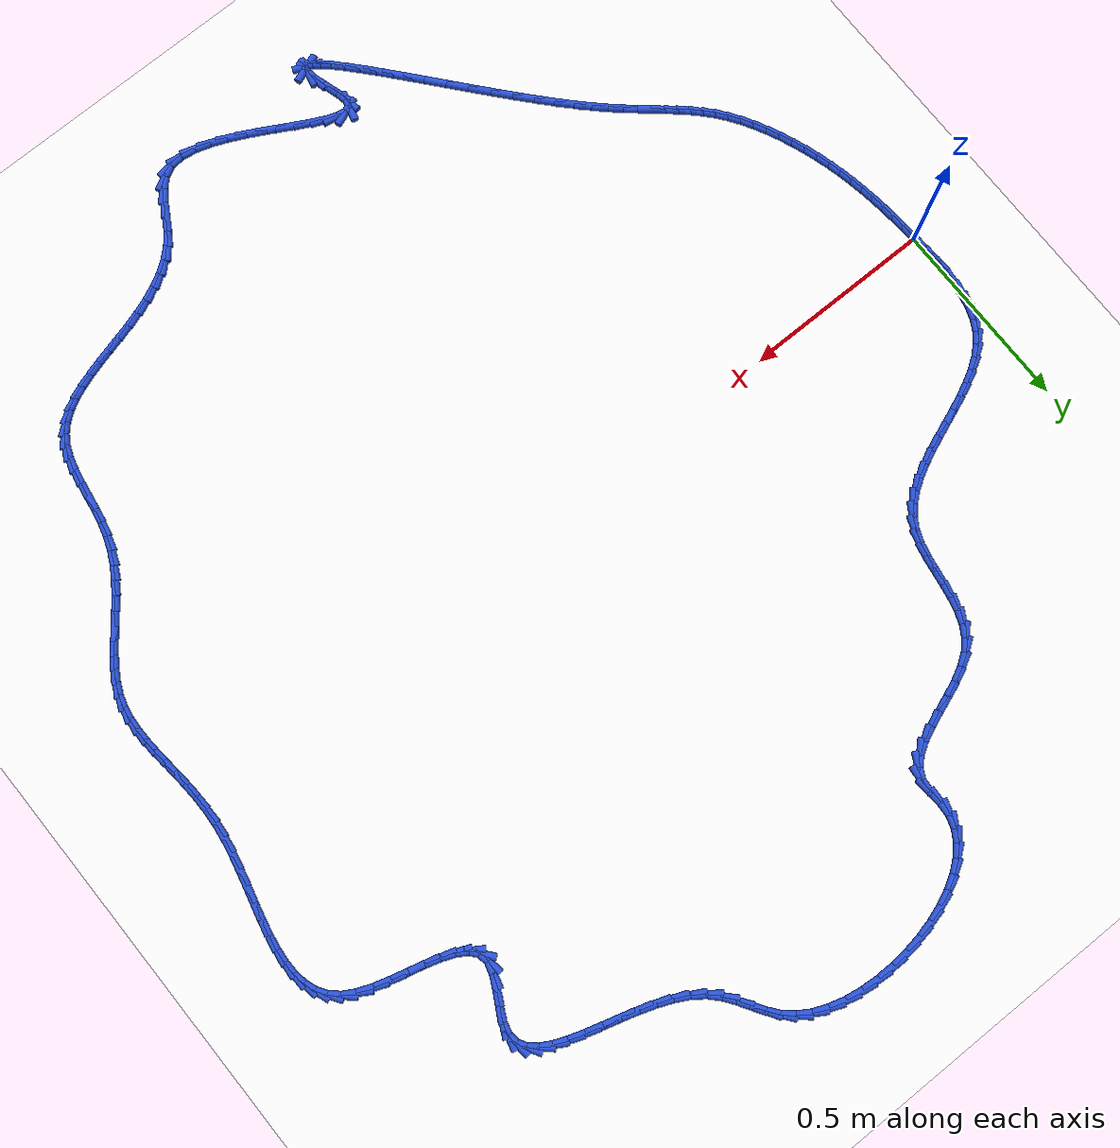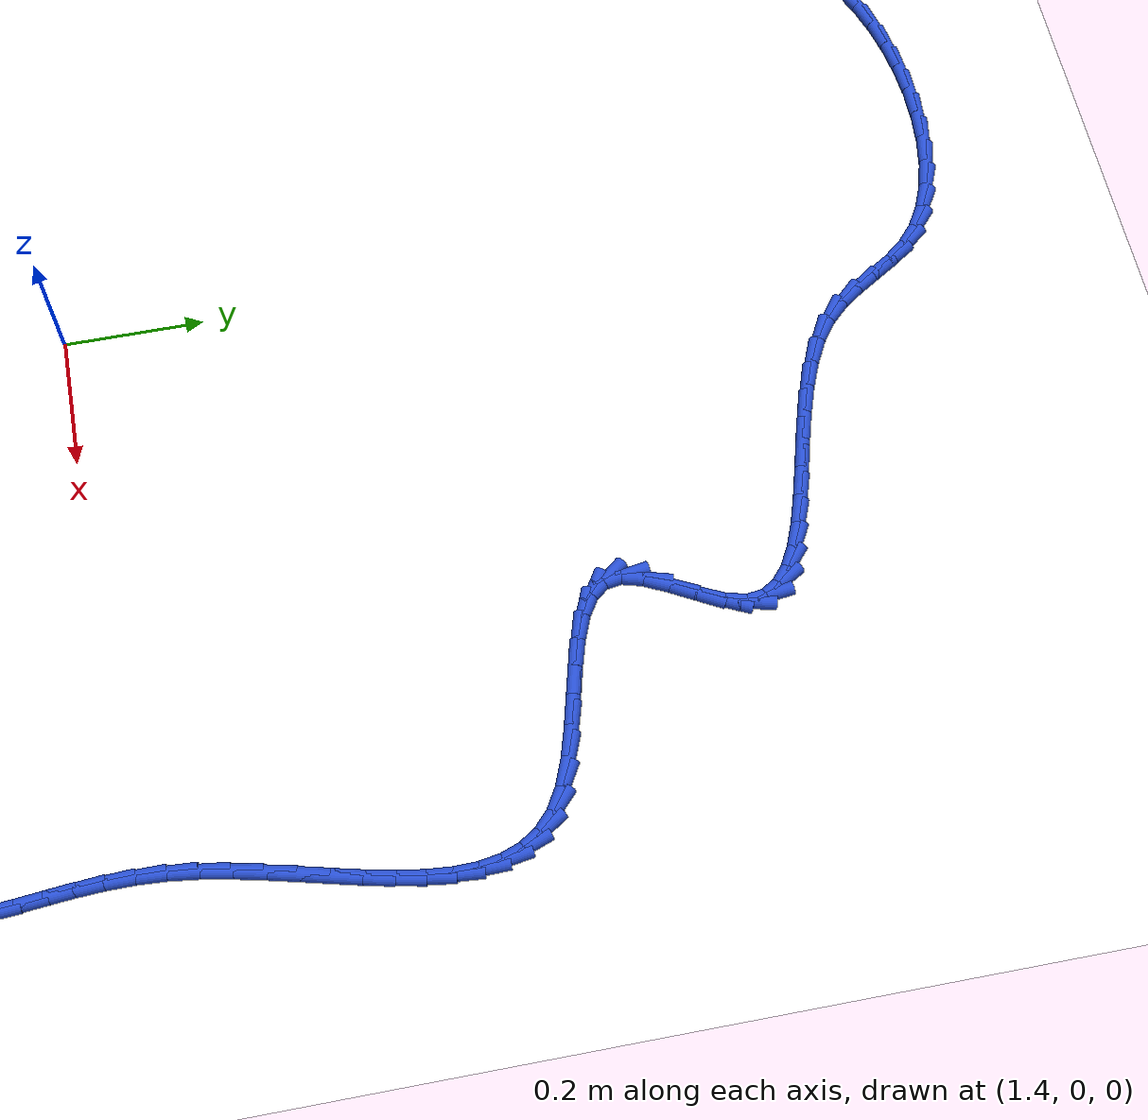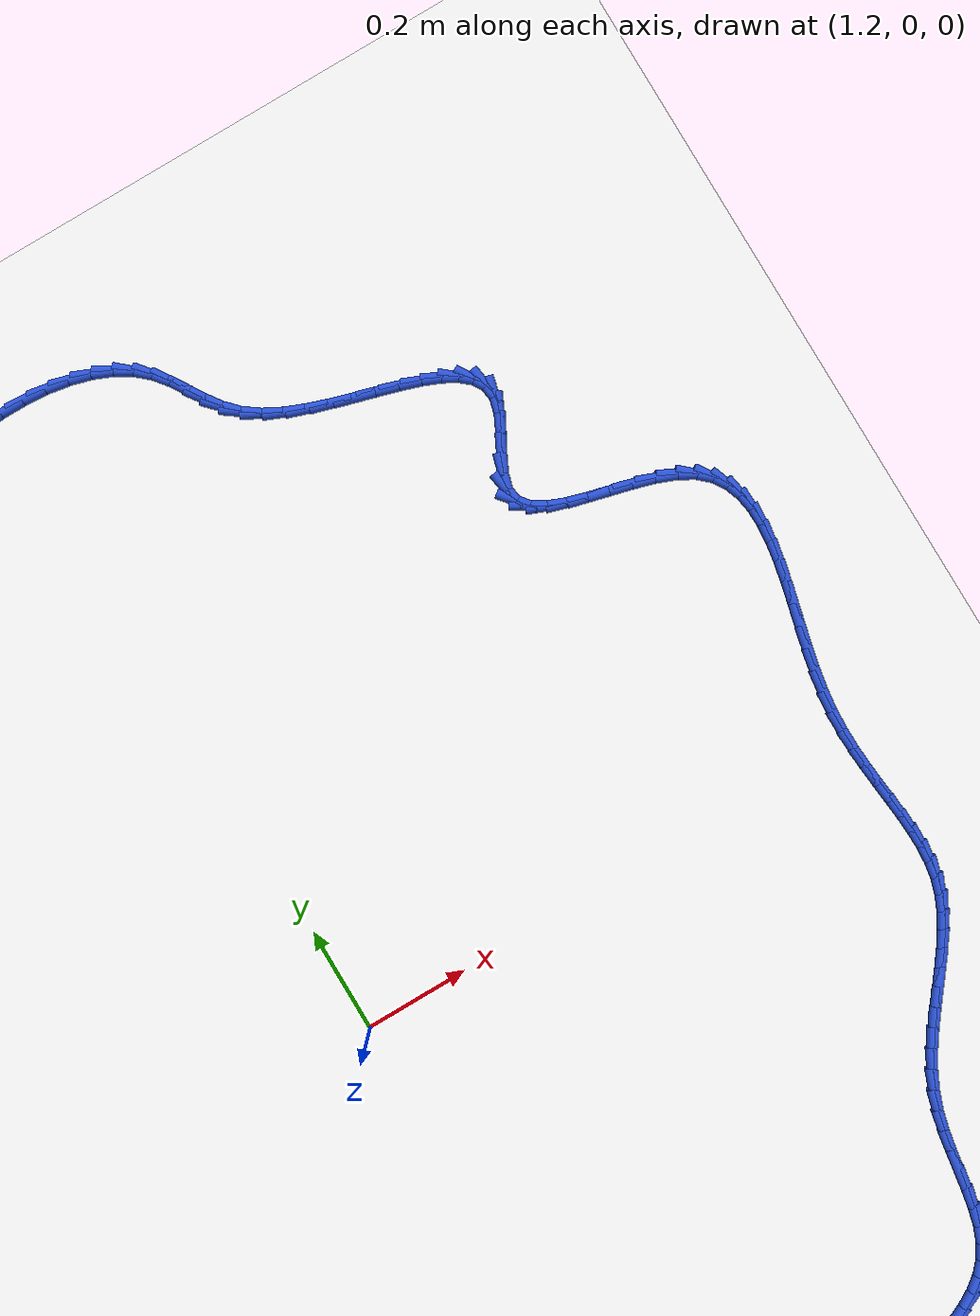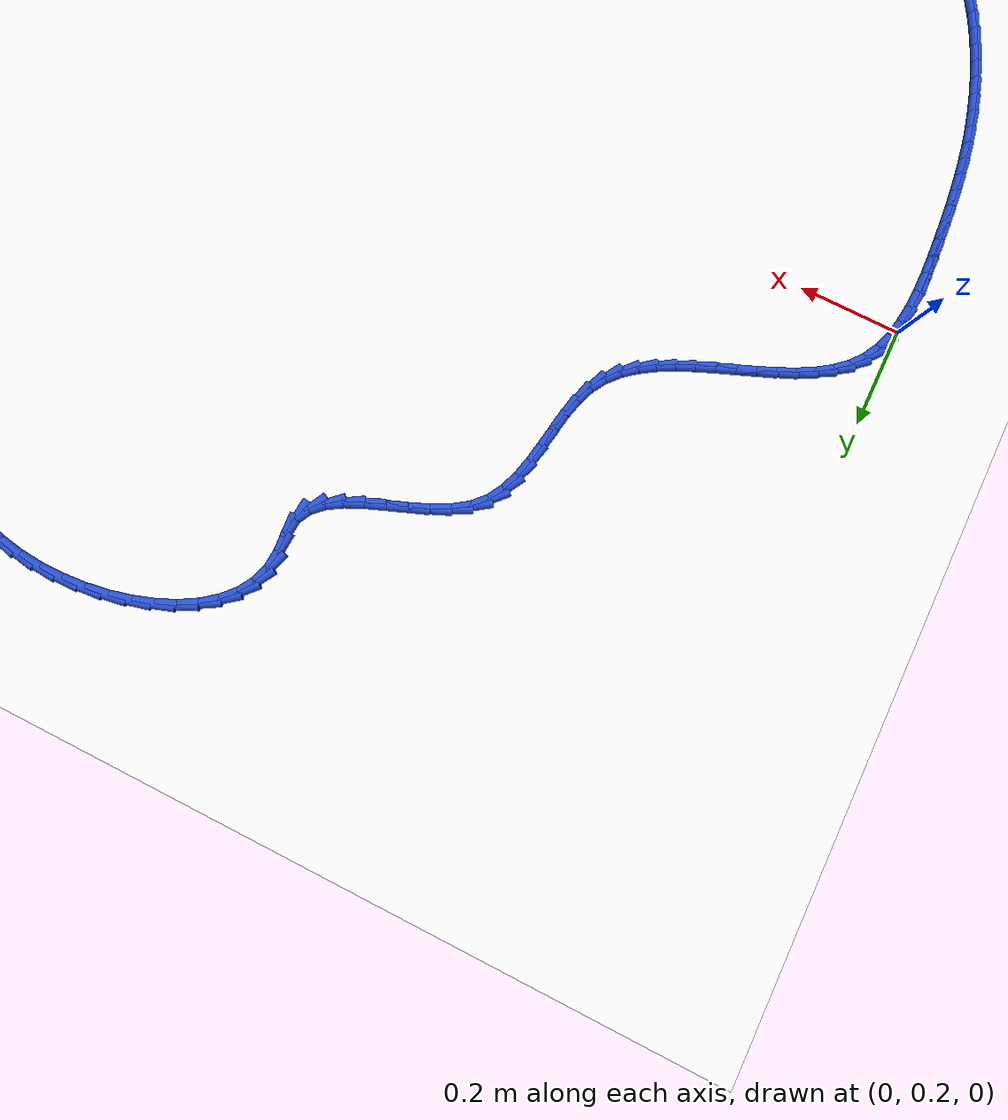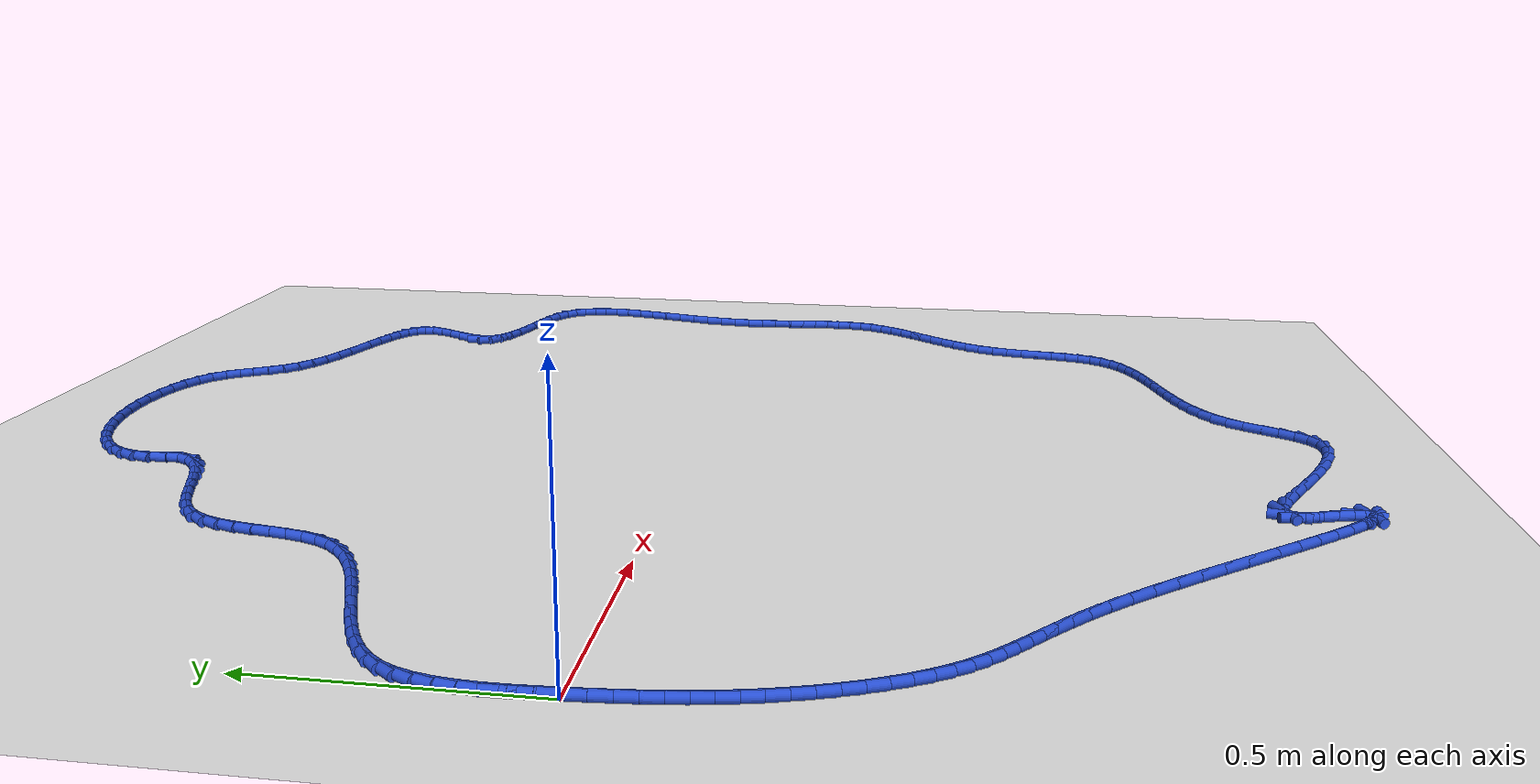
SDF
<sdf version="1.6">
 <world name="default">
  <light name="sun" type="directional">
   <pose>0 0 10 0 -0 0</pose>
   <diffuse>0.8 0.8 0.8 1</diffuse>
   <specular>0.2 0.2 0.2 1</specular>
   <attenuation>
    <range>1000</range>
    <constant>0.9</constant>
    <linear>0.01</linear>
    <quadratic>0.001</quadratic>
   </attenuation>
   <direction>-0.5 0.1 -0.9</direction>
  </light>
  <model name="ground_plane">
   <static>1</static>
   <link name="link">
    <collision name="collision">
     <geometry><plane><normal>0 0 1</normal><size>100 100</size></plane></geometry>
     <surface><friction><ode><mu>100</mu><mu2>50</mu2></ode></friction></surface>
    </collision>
    <visual name="visual">
     <cast_shadows>0</cast_shadows>
     <geometry><plane><normal>0 0 1</normal><size>100 100</size></plane></geometry>
     <material>
      <script><uri>file://media/materials/scripts/gazebo.material</uri><name>Gazebo/WhiteGlow</name></script>
     </material>
    </visual>
   </link>
  </model>
  <gravity>0 0 -9.8</gravity>
  <magnetic_field>6e-06 2.3e-05 -4.2e-05</magnetic_field>
  <atmosphere type="adiabatic"/>
  <physics name="default_physics" default="0" type="ode">
   <max_step_size>0.001</max_step_size>
   <real_time_factor>1</real_time_factor>
   <real_time_update_rate>1000</real_time_update_rate>
  </physics>
  <scene><ambient>0.4 0.4 0.4 1</ambient><background>0.7 0.7 0.7 1</background><shadows>1</shadows></scene>
  <spherical_coordinates>
   <surface_model>EARTH_WGS84</surface_model>
   <latitude_deg>0</latitude_deg>
   <longitude_deg>0</longitude_deg>
   <elevation>0</elevation>
   <heading_deg>0</heading_deg>
  </spherical_coordinates>
  <model name="line">
   <link name="link_0">
    <pose>-1.3010426069826053e-18 -7.632783294297951e-17 0.01 0 1.57 -1.5139232680995027</pose>
    <collision name="collision">
     <geometry><cylinder><radius>0.01</radius><length>0.08</length></cylinder></geometry>
    </collision>
    <visual name="visual">
     <material>
      <script><name>Gazebo/Blue</name><uri>file://media/materials/scripts/gazebo.material</uri></script>
     </material>
     <geometry><cylinder><radius>0.01</radius><length>0.08</length></cylinder></geometry>
    </visual>
   </link>
   <link name="link_1">
    <pose>-0.0021284036105607266 0.03738340013217717 0.01 0 1.57 -1.5364442885641492</pose>
    <collision name="collision">
     <geometry><cylinder><radius>0.01</radius><length>0.08</length></cylinder></geometry>
    </collision>
    <visual name="visual">
     <material>
      <script><name>Gazebo/Blue</name><uri>file://media/materials/scripts/gazebo.material</uri></script>
     </material>
     <geometry><cylinder><radius>0.01</radius><length>0.08</length></cylinder></geometry>
    </visual>
   </link>
   <link name="link_2">
    <pose>-0.0034273841131988586 0.07518230726856384 0.01 0 1.57 1.56781377270187</pose>
    <collision name="collision">
     <geometry><cylinder><radius>0.01</radius><length>0.08</length></cylinder></geometry>
    </collision>
    <visual name="visual">
     <material>
      <script><name>Gazebo/Blue</name><uri>file://media/materials/scripts/gazebo.material</uri></script>
     </material>
     <geometry><cylinder><radius>0.01</radius><length>0.08</length></cylinder></geometry>
    </visual>
   </link>
   <link name="link_3">
    <pose>-0.0033150827602514673 0.11283494203978386 0.01 0 1.57 1.5138687101963146</pose>
    <collision name="collision">
     <geometry><cylinder><radius>0.01</radius><length>0.08</length></cylinder></geometry>
    </collision>
    <visual name="visual">
     <material>
      <script><name>Gazebo/Blue</name><uri>file://media/materials/scripts/gazebo.material</uri></script>
     </material>
     <geometry><cylinder><radius>0.01</radius><length>0.08</length></cylinder></geometry>
    </visual>
   </link>
   <link name="link_4">
    <pose>-0.0012096408040556256 0.1497795250764612 0.01 0 1.57 1.4403438211716684</pose>
    <collision name="collision">
     <geometry><cylinder><radius>0.01</radius><length>0.08</length></cylinder></geometry>
    </collision>
    <visual name="visual">
     <material>
      <script><name>Gazebo/Blue</name><uri>file://media/materials/scripts/gazebo.material</uri></script>
     </material>
     <geometry><cylinder><radius>0.01</radius><length>0.08</length></cylinder></geometry>
    </visual>
   </link>
   <link name="link_5">
    <pose>0.0034708005030515982 0.18545427700921985 0.01 0 1.57 1.343230512753058</pose>
    <collision name="collision">
     <geometry><cylinder><radius>0.01</radius><length>0.08</length></cylinder></geometry>
    </collision>
    <visual name="visual">
     <material>
      <script><name>Gazebo/Blue</name><uri>file://media/materials/scripts/gazebo.material</uri></script>
     </material>
     <geometry><cylinder><radius>0.01</radius><length>0.08</length></cylinder></geometry>
    </visual>
   </link>
   <link name="link_6">
    <pose>0.011308099908733124 0.2192974184686838 0.01 0 1.57 1.2181064979412326</pose>
    <collision name="collision">
     <geometry><cylinder><radius>0.01</radius><length>0.08</length></cylinder></geometry>
    </collision>
    <visual name="visual">
     <material>
      <script><name>Gazebo/Blue</name><uri>file://media/materials/scripts/gazebo.material</uri></script>
     </material>
     <geometry><cylinder><radius>0.01</radius><length>0.08</length></cylinder></geometry>
    </visual>
   </link>
   <link name="link_7">
    <pose>0.022884116160651884 0.2507471700854769 0.01 0 1.57 1.0619224331731922</pose>
    <collision name="collision">
     <geometry><cylinder><radius>0.01</radius><length>0.08</length></cylinder></geometry>
    </collision>
    <visual name="visual">
     <material>
      <script><name>Gazebo/Blue</name><uri>file://media/materials/scripts/gazebo.material</uri></script>
     </material>
     <geometry><cylinder><radius>0.01</radius><length>0.08</length></cylinder></geometry>
    </visual>
   </link>
   <link name="link_8">
    <pose>0.038780708006470814 0.2792417524902233 0.01 0 1.57 0.8828282227197803</pose>
    <collision name="collision">
     <geometry><cylinder><radius>0.01</radius><length>0.08</length></cylinder></geometry>
    </collision>
    <visual name="visual">
     <material>
      <script><name>Gazebo/Blue</name><uri>file://media/materials/scripts/gazebo.material</uri></script>
     </material>
     <geometry><cylinder><radius>0.01</radius><length>0.08</length></cylinder></geometry>
    </visual>
   </link>
   <link name="link_9">
    <pose>0.0594199980144419 0.30435264336146 0.01 0 1.57 0.7226176003941184</pose>
    <collision name="collision">
     <geometry><cylinder><radius>0.01</radius><length>0.08</length></cylinder></geometry>
    </collision>
    <visual name="visual">
     <material>
      <script><name>Gazebo/Blue</name><uri>file://media/materials/scripts/gazebo.material</uri></script>
     </material>
     <geometry><cylinder><radius>0.01</radius><length>0.08</length></cylinder></geometry>
    </visual>
   </link>
   <link name="link_10">
    <pose>0.084377309043357 0.3263577478750683 0.01 0 1.57 0.5967472476528218</pose>
    <collision name="collision">
     <geometry><cylinder><radius>0.01</radius><length>0.08</length></cylinder></geometry>
    </collision>
    <visual name="visual">
     <material>
      <script><name>Gazebo/Blue</name><uri>file://media/materials/scripts/gazebo.material</uri></script>
     </material>
     <geometry><cylinder><radius>0.01</radius><length>0.08</length></cylinder></geometry>
    </visual>
   </link>
   <link name="link_11">
    <pose>0.11294842593145743 0.345768170795998 0.01 0 1.57 0.5031528593046318</pose>
    <collision name="collision">
     <geometry><cylinder><radius>0.01</radius><length>0.08</length></cylinder></geometry>
    </collision>
    <visual name="visual">
     <material>
      <script><name>Gazebo/Blue</name><uri>file://media/materials/scripts/gazebo.material</uri></script>
     </material>
     <geometry><cylinder><radius>0.01</radius><length>0.08</length></cylinder></geometry>
    </visual>
   </link>
   <link name="link_12">
    <pose>0.14442895878014725 0.3630951626602775 0.01 0 1.57 0.4374772014831631</pose>
    <collision name="collision">
     <geometry><cylinder><radius>0.01</radius><length>0.08</length></cylinder></geometry>
    </collision>
    <visual name="visual">
     <material>
      <script><name>Gazebo/Blue</name><uri>file://media/materials/scripts/gazebo.material</uri></script>
     </material>
     <geometry><cylinder><radius>0.01</radius><length>0.08</length></cylinder></geometry>
    </visual>
   </link>
   <link name="link_13">
    <pose>0.17811451769083034 0.37884997400393516 0.01 0 1.57 0.3955891787344779</pose>
    <collision name="collision">
     <geometry><cylinder><radius>0.01</radius><length>0.08</length></cylinder></geometry>
    </collision>
    <visual name="visual">
     <material>
      <script><name>Gazebo/Blue</name><uri>file://media/materials/scripts/gazebo.material</uri></script>
     </material>
     <geometry><cylinder><radius>0.01</radius><length>0.08</length></cylinder></geometry>
    </visual>
   </link>
   <link name="link_14">
    <pose>0.21330071276491064 0.3935438553629993 0.01 0 1.57 0.3745320510854445</pose>
    <collision name="collision">
     <geometry><cylinder><radius>0.01</radius><length>0.08</length></cylinder></geometry>
    </collision>
    <visual name="visual">
     <material>
      <script><name>Gazebo/Blue</name><uri>file://media/materials/scripts/gazebo.material</uri></script>
     </material>
     <geometry><cylinder><radius>0.01</radius><length>0.08</length></cylinder></geometry>
    </visual>
   </link>
   <link name="link_15">
    <pose>0.24928315410379207 0.4076880572734982 0.01 0 1.57 0.3727411345176775</pose>
    <collision name="collision">
     <geometry><cylinder><radius>0.01</radius><length>0.08</length></cylinder></geometry>
    </collision>
    <visual name="visual">
     <material>
      <script><name>Gazebo/Blue</name><uri>file://media/materials/scripts/gazebo.material</uri></script>
     </material>
     <geometry><cylinder><radius>0.01</radius><length>0.08</length></cylinder></geometry>
    </visual>
   </link>
   <link name="link_16">
    <pose>0.2853574518088786 0.4217938302714603 0.01 0 1.57 0.3900449206784528</pose>
    <collision name="collision">
     <geometry><cylinder><radius>0.01</radius><length>0.08</length></cylinder></geometry>
    </collision>
    <visual name="visual">
     <material>
      <script><name>Gazebo/Blue</name><uri>file://media/materials/scripts/gazebo.material</uri></script>
     </material>
     <geometry><cylinder><radius>0.01</radius><length>0.08</length></cylinder></geometry>
    </visual>
   </link>
   <link name="link_17">
    <pose>0.3208192159815742 0.43637242489291383 0.01 0 1.57 0.427653351015577</pose>
    <collision name="collision">
     <geometry><cylinder><radius>0.01</radius><length>0.08</length></cylinder></geometry>
    </collision>
    <visual name="visual">
     <material>
      <script><name>Gazebo/Blue</name><uri>file://media/materials/scripts/gazebo.material</uri></script>
     </material>
     <geometry><cylinder><radius>0.01</radius><length>0.08</length></cylinder></geometry>
    </visual>
   </link>
   <link name="link_18">
    <pose>0.3549640567232828 0.45193509167388723 0.01 0 1.57 0.48814858374382647</pose>
    <collision name="collision">
     <geometry><cylinder><radius>0.01</radius><length>0.08</length></cylinder></geometry>
    </collision>
    <visual name="visual">
     <material>
      <script><name>Gazebo/Blue</name><uri>file://media/materials/scripts/gazebo.material</uri></script>
     </material>
     <geometry><cylinder><radius>0.01</radius><length>0.08</length></cylinder></geometry>
    </visual>
   </link>
   <link name="link_19">
    <pose>0.3870875841354083 0.4689930811504088 0.01 0 1.57 0.5753217815755468</pose>
    <collision name="collision">
     <geometry><cylinder><radius>0.01</radius><length>0.08</length></cylinder></geometry>
    </collision>
    <visual name="visual">
     <material>
      <script><name>Gazebo/Blue</name><uri>file://media/materials/scripts/gazebo.material</uri></script>
     </material>
     <geometry><cylinder><radius>0.01</radius><length>0.08</length></cylinder></geometry>
    </visual>
   </link>
   <link name="link_20">
    <pose>0.41648540831935466 0.4880576438585068 0.01 0 1.57 0.6934325791270846</pose>
    <collision name="collision">
     <geometry><cylinder><radius>0.01</radius><length>0.08</length></cylinder></geometry>
    </collision>
    <visual name="visual">
     <material>
      <script><name>Gazebo/Blue</name><uri>file://media/materials/scripts/gazebo.material</uri></script>
     </material>
     <geometry><cylinder><radius>0.01</radius><length>0.08</length></cylinder></geometry>
    </visual>
   </link>
   <link name="link_21">
    <pose>0.44245313937652575 0.5096400303342095 0.01 0 1.57 0.8451446080196746</pose>
    <collision name="collision">
     <geometry><cylinder><radius>0.01</radius><length>0.08</length></cylinder></geometry>
    </collision>
    <visual name="visual">
     <material>
      <script><name>Gazebo/Blue</name><uri>file://media/materials/scripts/gazebo.material</uri></script>
     </material>
     <geometry><cylinder><radius>0.01</radius><length>0.08</length></cylinder></geometry>
    </visual>
   </link>
   <link name="link_22">
    <pose>0.4642863874083254 0.5342514911135454 0.01 0 1.57 1.0274688767504392</pose>
    <collision name="collision">
     <geometry><cylinder><radius>0.01</radius><length>0.08</length></cylinder></geometry>
    </collision>
    <visual name="visual">
     <material>
      <script><name>Gazebo/Blue</name><uri>file://media/materials/scripts/gazebo.material</uri></script>
     </material>
     <geometry><cylinder><radius>0.01</radius><length>0.08</length></cylinder></geometry>
    </visual>
   </link>
   <link name="link_23">
    <pose>0.4812865397188464 0.5623992218726417 0.01 0 1.57 1.2050323884709566</pose>
    <collision name="collision">
     <geometry><cylinder><radius>0.01</radius><length>0.08</length></cylinder></geometry>
    </collision>
    <visual name="visual">
     <material>
      <script><name>Gazebo/Blue</name><uri>file://media/materials/scripts/gazebo.material</uri></script>
     </material>
     <geometry><cylinder><radius>0.01</radius><length>0.08</length></cylinder></geometry>
    </visual>
   </link>
   <link name="link_24">
    <pose>0.49343334342494405 0.5941142961655922 0.01 0 1.57 1.3263492876451688</pose>
    <collision name="collision">
     <geometry><cylinder><radius>0.01</radius><length>0.08</length></cylinder></geometry>
    </collision>
    <visual name="visual">
     <material>
      <script><name>Gazebo/Blue</name><uri>file://media/materials/scripts/gazebo.material</uri></script>
     </material>
     <geometry><cylinder><radius>0.01</radius><length>0.08</length></cylinder></geometry>
    </visual>
   </link>
   <link name="link_25">
    <pose>0.5020130415698378 0.6285107939375185 0.01 0 1.57 1.3940018542698362</pose>
    <collision name="collision">
     <geometry><cylinder><radius>0.01</radius><length>0.08</length></cylinder></geometry>
    </collision>
    <visual name="visual">
     <material>
      <script><name>Gazebo/Blue</name><uri>file://media/materials/scripts/gazebo.material</uri></script>
     </material>
     <geometry><cylinder><radius>0.01</radius><length>0.08</length></cylinder></geometry>
    </visual>
   </link>
   <link name="link_26">
    <pose>0.5084604641471484 0.6645985060338632 0.01 0 1.57 1.4157534171334576</pose>
    <collision name="collision">
     <geometry><cylinder><radius>0.01</radius><length>0.08</length></cylinder></geometry>
    </collision>
    <visual name="visual">
     <material>
      <script><name>Gazebo/Blue</name><uri>file://media/materials/scripts/gazebo.material</uri></script>
     </material>
     <geometry><cylinder><radius>0.01</radius><length>0.08</length></cylinder></geometry>
    </visual>
   </link>
   <link name="link_27">
    <pose>0.5142104411504966 0.7013872233000685 0.01 0 1.57 1.3948949704035905</pose>
    <collision name="collision">
     <geometry><cylinder><radius>0.01</radius><length>0.08</length></cylinder></geometry>
    </collision>
    <visual name="visual">
     <material>
      <script><name>Gazebo/Blue</name><uri>file://media/materials/scripts/gazebo.material</uri></script>
     </material>
     <geometry><cylinder><radius>0.01</radius><length>0.08</length></cylinder></geometry>
    </visual>
   </link>
   <link name="link_28">
    <pose>0.5206978025735035 0.737886736581577 0.01 0 1.57 1.3297082210671192</pose>
    <collision name="collision">
     <geometry><cylinder><radius>0.01</radius><length>0.08</length></cylinder></geometry>
    </collision>
    <visual name="visual">
     <material>
      <script><name>Gazebo/Blue</name><uri>file://media/materials/scripts/gazebo.material</uri></script>
     </material>
     <geometry><cylinder><radius>0.01</radius><length>0.08</length></cylinder></geometry>
    </visual>
   </link>
   <link name="link_29">
    <pose>0.5293573784097897 0.7731068367238311 0.01 0 1.57 1.2144173390147066</pose>
    <collision name="collision">
     <geometry><cylinder><radius>0.01</radius><length>0.08</length></cylinder></geometry>
    </collision>
    <visual name="visual">
     <material>
      <script><name>Gazebo/Blue</name><uri>file://media/materials/scripts/gazebo.material</uri></script>
     </material>
     <geometry><cylinder><radius>0.01</radius><length>0.08</length></cylinder></geometry>
    </visual>
   </link>
   <link name="link_30">
    <pose>0.5416239986529761 0.8060573145722731 0.01 0 1.57 1.0429995825151954</pose>
    <collision name="collision">
     <geometry><cylinder><radius>0.01</radius><length>0.08</length></cylinder></geometry>
    </collision>
    <visual name="visual">
     <material>
      <script><name>Gazebo/Blue</name><uri>file://media/materials/scripts/gazebo.material</uri></script>
     </material>
     <geometry><cylinder><radius>0.01</radius><length>0.08</length></cylinder></geometry>
    </visual>
   </link>
   <link name="link_31">
    <pose>0.5589324932966835 0.8357479609723459 0.01 0 1.57 0.8199587072185819</pose>
    <collision name="collision">
     <geometry><cylinder><radius>0.01</radius><length>0.08</length></cylinder></geometry>
    </collision>
    <visual name="visual">
     <material>
      <script><name>Gazebo/Blue</name><uri>file://media/materials/scripts/gazebo.material</uri></script>
     </material>
     <geometry><cylinder><radius>0.01</radius><length>0.08</length></cylinder></geometry>
    </visual>
   </link>
   <link name="link_32">
    <pose>0.5826893421267202 0.8612063942453018 0.01 0 1.57 0.6083904212454403</pose>
    <collision name="collision">
     <geometry><cylinder><radius>0.01</radius><length>0.08</length></cylinder></geometry>
    </collision>
    <visual name="visual">
     <material>
      <script><name>Gazebo/Blue</name><uri>file://media/materials/scripts/gazebo.material</uri></script>
     </material>
     <geometry><cylinder><radius>0.01</radius><length>0.08</length></cylinder></geometry>
    </visual>
   </link>
   <link name="link_33">
    <pose>0.6129696760879733 0.8822974254911249 0.01 0 1.57 0.469702103577251</pose>
    <collision name="collision">
     <geometry><cylinder><radius>0.01</radius><length>0.08</length></cylinder></geometry>
    </collision>
    <visual name="visual">
     <material>
      <script><name>Gazebo/Blue</name><uri>file://media/materials/scripts/gazebo.material</uri></script>
     </material>
     <geometry><cylinder><radius>0.01</radius><length>0.08</length></cylinder></geometry>
    </visual>
   </link>
   <link name="link_34">
    <pose>0.6479734508677638 0.9000650332347762 0.01 0 1.57 0.3910132116865285</pose>
    <collision name="collision">
     <geometry><cylinder><radius>0.01</radius><length>0.08</length></cylinder></geometry>
    </collision>
    <visual name="visual">
     <material>
      <script><name>Gazebo/Blue</name><uri>file://media/materials/scripts/gazebo.material</uri></script>
     </material>
     <geometry><cylinder><radius>0.01</radius><length>0.08</length></cylinder></geometry>
    </visual>
   </link>
   <link name="link_35">
    <pose>0.6857594909900793 0.915641943583489 0.01 0 1.57 0.35953681462104947</pose>
    <collision name="collision">
     <geometry><cylinder><radius>0.01</radius><length>0.08</length></cylinder></geometry>
    </collision>
    <visual name="visual">
     <material>
      <script><name>Gazebo/Blue</name><uri>file://media/materials/scripts/gazebo.material</uri></script>
     </material>
     <geometry><cylinder><radius>0.01</radius><length>0.08</length></cylinder></geometry>
    </visual>
   </link>
   <link name="link_36">
    <pose>0.7243866209789083 0.9301608826444987 0.01 0 1.57 0.3708876614324501</pose>
    <collision name="collision">
     <geometry><cylinder><radius>0.01</radius><length>0.08</length></cylinder></geometry>
    </collision>
    <visual name="visual">
     <material>
      <script><name>Gazebo/Blue</name><uri>file://media/materials/scripts/gazebo.material</uri></script>
     </material>
     <geometry><cylinder><radius>0.01</radius><length>0.08</length></cylinder></geometry>
    </visual>
   </link>
   <link name="link_37">
    <pose>0.7619136653582389 0.9447545765250394 0.01 0 1.57 0.4296470278583007</pose>
    <collision name="collision">
     <geometry><cylinder><radius>0.01</radius><length>0.08</length></cylinder></geometry>
    </collision>
    <visual name="visual">
     <material>
      <script><name>Gazebo/Blue</name><uri>file://media/materials/scripts/gazebo.material</uri></script>
     </material>
     <geometry><cylinder><radius>0.01</radius><length>0.08</length></cylinder></geometry>
    </visual>
   </link>
   <link name="link_38">
    <pose>0.796399448652059 0.9605557513323455 0.01 0 1.57 0.5512978442683394</pose>
    <collision name="collision">
     <geometry><cylinder><radius>0.01</radius><length>0.08</length></cylinder></geometry>
    </collision>
    <visual name="visual">
     <material>
      <script><name>Gazebo/Blue</name><uri>file://media/materials/scripts/gazebo.material</uri></script>
     </material>
     <geometry><cylinder><radius>0.01</radius><length>0.08</length></cylinder></geometry>
    </visual>
   </link>
   <link name="link_39">
    <pose>0.8259027953843573 0.9786971331736517 0.01 0 1.57 0.7635566214791604</pose>
    <collision name="collision">
     <geometry><cylinder><radius>0.01</radius><length>0.08</length></cylinder></geometry>
    </collision>
    <visual name="visual">
     <material>
      <script><name>Gazebo/Blue</name><uri>file://media/materials/scripts/gazebo.material</uri></script>
     </material>
     <geometry><cylinder><radius>0.01</radius><length>0.08</length></cylinder></geometry>
    </visual>
   </link>
   <link name="link_40">
    <pose>0.8484825300791218 1.0003114481561928 0.01 0 1.57 1.088861556387261</pose>
    <collision name="collision">
     <geometry><cylinder><radius>0.01</radius><length>0.08</length></cylinder></geometry>
    </collision>
    <visual name="visual">
     <material>
      <script><name>Gazebo/Blue</name><uri>file://media/materials/scripts/gazebo.material</uri></script>
     </material>
     <geometry><cylinder><radius>0.01</radius><length>0.08</length></cylinder></geometry>
    </visual>
   </link>
   <link name="link_41">
    <pose>0.8621974772603399 1.0265314223872022 0.01 0 1.57 1.4735262635273387</pose>
    <collision name="collision">
     <geometry><cylinder><radius>0.01</radius><length>0.08</length></cylinder></geometry>
    </collision>
    <visual name="visual">
     <material>
      <script><name>Gazebo/Blue</name><uri>file://media/materials/scripts/gazebo.material</uri></script>
     </material>
     <geometry><cylinder><radius>0.01</radius><length>0.08</length></cylinder></geometry>
    </visual>
   </link>
   <link name="link_42">
    <pose>0.865307034237414 1.0583988201567092 0.01 0 1.57 -1.4897214137696533</pose>
    <collision name="collision">
     <geometry><cylinder><radius>0.01</radius><length>0.08</length></cylinder></geometry>
    </collision>
    <visual name="visual">
     <material>
      <script><name>Gazebo/Blue</name><uri>file://media/materials/scripts/gazebo.material</uri></script>
     </material>
     <geometry><cylinder><radius>0.01</radius><length>0.08</length></cylinder></geometry>
    </visual>
   </link>
   <link name="link_43">
    <pose>0.8624077120073235 1.094081459642477 0.01 0 1.57 1.5092702640326205</pose>
    <collision name="collision">
     <geometry><cylinder><radius>0.01</radius><length>0.08</length></cylinder></geometry>
    </collision>
    <visual name="visual">
     <material>
      <script><name>Gazebo/Blue</name><uri>file://media/materials/scripts/gazebo.material</uri></script>
     </material>
     <geometry><cylinder><radius>0.01</radius><length>0.08</length></cylinder></geometry>
    </visual>
   </link>
   <link name="link_44">
    <pose>0.8645444560755889 1.1287667150928553 0.01 0 1.57 1.2576299831816027</pose>
    <collision name="collision">
     <geometry><cylinder><radius>0.01</radius><length>0.08</length></cylinder></geometry>
    </collision>
    <visual name="visual">
     <material>
      <script><name>Gazebo/Blue</name><uri>file://media/materials/scripts/gazebo.material</uri></script>
     </material>
     <geometry><cylinder><radius>0.01</radius><length>0.08</length></cylinder></geometry>
    </visual>
   </link>
   <link name="link_45">
    <pose>0.8749026464699916 1.1607539819064296 0.01 0 1.57 1.0242996294956264</pose>
    <collision name="collision">
     <geometry><cylinder><radius>0.01</radius><length>0.08</length></cylinder></geometry>
    </collision>
    <visual name="visual">
     <material>
      <script><name>Gazebo/Blue</name><uri>file://media/materials/scripts/gazebo.material</uri></script>
     </material>
     <geometry><cylinder><radius>0.01</radius><length>0.08</length></cylinder></geometry>
    </visual>
   </link>
   <link name="link_46">
    <pose>0.8926577947002398 1.1899423500149016 0.01 0 1.57 0.8248542132630601</pose>
    <collision name="collision">
     <geometry><cylinder><radius>0.01</radius><length>0.08</length></cylinder></geometry>
    </collision>
    <visual name="visual">
     <material>
      <script><name>Gazebo/Blue</name><uri>file://media/materials/scripts/gazebo.material</uri></script>
     </material>
     <geometry><cylinder><radius>0.01</radius><length>0.08</length></cylinder></geometry>
    </visual>
   </link>
   <link name="link_47">
    <pose>0.9169592574291473 1.2162413435488524 0.01 0 1.57 0.6607946753579317</pose>
    <collision name="collision">
     <geometry><cylinder><radius>0.01</radius><length>0.08</length></cylinder></geometry>
    </collision>
    <visual name="visual">
     <material>
      <script><name>Gazebo/Blue</name><uri>file://media/materials/scripts/gazebo.material</uri></script>
     </material>
     <geometry><cylinder><radius>0.01</radius><length>0.08</length></cylinder></geometry>
    </visual>
   </link>
   <link name="link_48">
    <pose>0.9469563913195265 1.2395604866388612 0.01 0 1.57 0.5264502032049996</pose>
    <collision name="collision">
     <geometry><cylinder><radius>0.01</radius><length>0.08</length></cylinder></geometry>
    </collision>
    <visual name="visual">
     <material>
      <script><name>Gazebo/Blue</name><uri>file://media/materials/scripts/gazebo.material</uri></script>
     </material>
     <geometry><cylinder><radius>0.01</radius><length>0.08</length></cylinder></geometry>
    </visual>
   </link>
   <link name="link_49">
    <pose>0.981798553034191 1.2598093034155093 0.01 0 1.57 0.41450545651724247</pose>
    <collision name="collision">
     <geometry><cylinder><radius>0.01</radius><length>0.08</length></cylinder></geometry>
    </collision>
    <visual name="visual">
     <material>
      <script><name>Gazebo/Blue</name><uri>file://media/materials/scripts/gazebo.material</uri></script>
     </material>
     <geometry><cylinder><radius>0.01</radius><length>0.08</length></cylinder></geometry>
    </visual>
   </link>
   <link name="link_50">
    <pose>1.0206350992359539 1.2768973180093774 0.01 0 1.57 0.3183875265638465</pose>
    <collision name="collision">
     <geometry><cylinder><radius>0.01</radius><length>0.08</length></cylinder></geometry>
    </collision>
    <visual name="visual">
     <material>
      <script><name>Gazebo/Blue</name><uri>file://media/materials/scripts/gazebo.material</uri></script>
     </material>
     <geometry><cylinder><radius>0.01</radius><length>0.08</length></cylinder></geometry>
    </visual>
   </link>
   <link name="link_51">
    <pose>1.0626153865876282 1.2907340545510457 0.01 0 1.57 0.23275328609844836</pose>
    <collision name="collision">
     <geometry><cylinder><radius>0.01</radius><length>0.08</length></cylinder></geometry>
    </collision>
    <visual name="visual">
     <material>
      <script><name>Gazebo/Blue</name><uri>file://media/materials/scripts/gazebo.material</uri></script>
     </material>
     <geometry><cylinder><radius>0.01</radius><length>0.08</length></cylinder></geometry>
    </visual>
   </link>
   <link name="link_52">
    <pose>1.106888771752027 1.3012290371710944 0.01 0 1.57 0.15328063610386292</pose>
    <collision name="collision">
     <geometry><cylinder><radius>0.01</radius><length>0.08</length></cylinder></geometry>
    </collision>
    <visual name="visual">
     <material>
      <script><name>Gazebo/Blue</name><uri>file://media/materials/scripts/gazebo.material</uri></script>
     </material>
     <geometry><cylinder><radius>0.01</radius><length>0.08</length></cylinder></geometry>
    </visual>
   </link>
   <link name="link_53">
    <pose>1.1526046113919635 1.3082917900001034 0.01 0 1.57 0.07629787171832753</pose>
    <collision name="collision">
     <geometry><cylinder><radius>0.01</radius><length>0.08</length></cylinder></geometry>
    </collision>
    <visual name="visual">
     <material>
      <script><name>Gazebo/Blue</name><uri>file://media/materials/scripts/gazebo.material</uri></script>
     </material>
     <geometry><cylinder><radius>0.01</radius><length>0.08</length></cylinder></geometry>
    </visual>
   </link>
   <link name="link_54">
    <pose>1.1989122621702508 1.3118318371686541 0.01 0 1.57 -0.0015881905788877727</pose>
    <collision name="collision">
     <geometry><cylinder><radius>0.01</radius><length>0.08</length></cylinder></geometry>
    </collision>
    <visual name="visual">
     <material>
      <script><name>Gazebo/Blue</name><uri>file://media/materials/scripts/gazebo.material</uri></script>
     </material>
     <geometry><cylinder><radius>0.01</radius><length>0.08</length></cylinder></geometry>
    </visual>
   </link>
   <link name="link_55">
    <pose>1.2449610807497025 1.3117587028073272 0.01 0 1.57 -0.0838449585973191</pose>
    <collision name="collision">
     <geometry><cylinder><radius>0.01</radius><length>0.08</length></cylinder></geometry>
    </collision>
    <visual name="visual">
     <material>
      <script><name>Gazebo/Blue</name><uri>file://media/materials/scripts/gazebo.material</uri></script>
     </material>
     <geometry><cylinder><radius>0.01</radius><length>0.08</length></cylinder></geometry>
    </visual>
   </link>
   <link name="link_56">
    <pose>1.2899004237931302 1.3079819110467024 0.01 0 1.57 -0.17436431548379694</pose>
    <collision name="collision">
     <geometry><cylinder><radius>0.01</radius><length>0.08</length></cylinder></geometry>
    </collision>
    <visual name="visual">
     <material>
      <script><name>Gazebo/Blue</name><uri>file://media/materials/scripts/gazebo.material</uri></script>
     </material>
     <geometry><cylinder><radius>0.01</radius><length>0.08</length></cylinder></geometry>
    </visual>
   </link>
   <link name="link_57">
    <pose>1.3328796479633491 1.3004109860173598 0.01 0 1.57 -0.27781235396920373</pose>
    <collision name="collision">
     <geometry><cylinder><radius>0.01</radius><length>0.08</length></cylinder></geometry>
    </collision>
    <visual name="visual">
     <material>
      <script><name>Gazebo/Blue</name><uri>file://media/materials/scripts/gazebo.material</uri></script>
     </material>
     <geometry><cylinder><radius>0.01</radius><length>0.08</length></cylinder></geometry>
    </visual>
   </link>
   <link name="link_58">
    <pose>1.3730481099231708 1.288955451849881 0.01 0 1.57 -0.3998996837076831</pose>
    <collision name="collision">
     <geometry><cylinder><radius>0.01</radius><length>0.08</length></cylinder></geometry>
    </collision>
    <visual name="visual">
     <material>
      <script><name>Gazebo/Blue</name><uri>file://media/materials/scripts/gazebo.material</uri></script>
     </material>
     <geometry><cylinder><radius>0.01</radius><length>0.08</length></cylinder></geometry>
    </visual>
   </link>
   <link name="link_59">
    <pose>1.4095551663354096 1.2735248326748456 0.01 0 1.57 -0.5472666567409499</pose>
    <collision name="collision">
     <geometry><cylinder><radius>0.01</radius><length>0.08</length></cylinder></geometry>
    </collision>
    <visual name="visual">
     <material>
      <script><name>Gazebo/Blue</name><uri>file://media/materials/scripts/gazebo.material</uri></script>
     </material>
     <geometry><cylinder><radius>0.01</radius><length>0.08</length></cylinder></geometry>
    </visual>
   </link>
   <link name="link_60">
    <pose>1.4415501738628773 1.2540286526228344 0.01 0 1.57 -0.7255798642377025</pose>
    <collision name="collision">
     <geometry><cylinder><radius>0.01</radius><length>0.08</length></cylinder></geometry>
    </collision>
    <visual name="visual">
     <material>
      <script><name>Gazebo/Blue</name><uri>file://media/materials/scripts/gazebo.material</uri></script>
     </material>
     <geometry><cylinder><radius>0.01</radius><length>0.08</length></cylinder></geometry>
    </visual>
   </link>
   <link name="link_61">
    <pose>1.4682036106717167 1.2303873548578907 0.01 0 1.57 -0.8983669218169948</pose>
    <collision name="collision">
     <geometry><cylinder><radius>0.01</radius><length>0.08</length></cylinder></geometry>
    </collision>
    <visual name="visual">
     <material>
      <script><name>Gazebo/Blue</name><uri>file://media/materials/scripts/gazebo.material</uri></script>
     </material>
     <geometry><cylinder><radius>0.01</radius><length>0.08</length></cylinder></geometry>
    </visual>
   </link>
   <link name="link_62">
    <pose>1.4898937854657486 1.2031457861129788 0.01 0 1.57 -0.9975713345431633</pose>
    <collision name="collision">
     <geometry><cylinder><radius>0.01</radius><length>0.08</length></cylinder></geometry>
    </collision>
    <visual name="visual">
     <material>
      <script><name>Gazebo/Blue</name><uri>file://media/materials/scripts/gazebo.material</uri></script>
     </material>
     <geometry><cylinder><radius>0.01</radius><length>0.08</length></cylinder></geometry>
    </visual>
   </link>
   <link name="link_63">
    <pose>1.5088377325551274 1.1737993460298015 0.01 0 1.57 -1.0146920540075322</pose>
    <collision name="collision">
     <geometry><cylinder><radius>0.01</radius><length>0.08</length></cylinder></geometry>
    </collision>
    <visual name="visual">
     <material>
      <script><name>Gazebo/Blue</name><uri>file://media/materials/scripts/gazebo.material</uri></script>
     </material>
     <geometry><cylinder><radius>0.01</radius><length>0.08</length></cylinder></geometry>
    </visual>
   </link>
   <link name="link_64">
    <pose>1.5274068145716095 1.1439232162656576 0.01 0 1.57 -0.9511840860194475</pose>
    <collision name="collision">
     <geometry><cylinder><radius>0.01</radius><length>0.08</length></cylinder></geometry>
    </collision>
    <visual name="visual">
     <material>
      <script><name>Gazebo/Blue</name><uri>file://media/materials/scripts/gazebo.material</uri></script>
     </material>
     <geometry><cylinder><radius>0.01</radius><length>0.08</length></cylinder></geometry>
    </visual>
   </link>
   <link name="link_65">
    <pose>1.5479723941469505 1.1150925784778454 0.01 0 1.57 -0.8103622688936618</pose>
    <collision name="collision">
     <geometry><cylinder><radius>0.01</radius><length>0.08</length></cylinder></geometry>
    </collision>
    <visual name="visual">
     <material>
      <script><name>Gazebo/Blue</name><uri>file://media/materials/scripts/gazebo.material</uri></script>
     </material>
     <geometry><cylinder><radius>0.01</radius><length>0.08</length></cylinder></geometry>
    </visual>
   </link>
   <link name="link_66">
    <pose>1.5729055293670693 1.0888824316782764 0.01 0 1.57 -0.6290478197523717</pose>
    <collision name="collision">
     <geometry><cylinder><radius>0.01</radius><length>0.08</length></cylinder></geometry>
    </collision>
    <visual name="visual">
     <material>
      <script><name>Gazebo/Blue</name><uri>file://media/materials/scripts/gazebo.material</uri></script>
     </material>
     <geometry><cylinder><radius>0.01</radius><length>0.08</length></cylinder></geometry>
    </visual>
   </link>
   <link name="link_67">
    <pose>1.6038001693990729 1.0664017190601867 0.01 0 1.57 -0.488207788068272</pose>
    <collision name="collision">
     <geometry><cylinder><radius>0.01</radius><length>0.08</length></cylinder></geometry>
    </collision>
    <visual name="visual">
     <material>
      <script><name>Gazebo/Blue</name><uri>file://media/materials/scripts/gazebo.material</uri></script>
     </material>
     <geometry><cylinder><radius>0.01</radius><length>0.08</length></cylinder></geometry>
    </visual>
   </link>
   <link name="link_68">
    <pose>1.6397935850909031 1.0472860392218066 0.01 0 1.57 -0.3914636212559159</pose>
    <collision name="collision">
     <geometry><cylinder><radius>0.01</radius><length>0.08</length></cylinder></geometry>
    </collision>
    <visual name="visual">
     <material>
      <script><name>Gazebo/Blue</name><uri>file://media/materials/scripts/gazebo.material</uri></script>
     </material>
     <geometry><cylinder><radius>0.01</radius><length>0.08</length></cylinder></geometry>
    </visual>
   </link>
   <link name="link_69">
    <pose>1.6795387588245427 1.0308805482609498 0.01 0 1.57 -0.32814623787620967</pose>
    <collision name="collision">
     <geometry><cylinder><radius>0.01</radius><length>0.08</length></cylinder></geometry>
    </collision>
    <visual name="visual">
     <material>
      <script><name>Gazebo/Blue</name><uri>file://media/materials/scripts/gazebo.material</uri></script>
     </material>
     <geometry><cylinder><radius>0.01</radius><length>0.08</length></cylinder></geometry>
    </visual>
   </link>
   <link name="link_70">
    <pose>1.7216886729819731 1.0165304022754262 0.01 0 1.57 -0.29118825557874933</pose>
    <collision name="collision">
     <geometry><cylinder><radius>0.01</radius><length>0.08</length></cylinder></geometry>
    </collision>
    <visual name="visual">
     <material>
      <script><name>Gazebo/Blue</name><uri>file://media/materials/scripts/gazebo.material</uri></script>
     </material>
     <geometry><cylinder><radius>0.01</radius><length>0.08</length></cylinder></geometry>
    </visual>
   </link>
   <link name="link_71">
    <pose>1.7648963099451769 1.0035807573630493 0.01 0 1.57 -0.277041271911529</pose>
    <collision name="collision">
     <geometry><cylinder><radius>0.01</radius><length>0.08</length></cylinder></geometry>
    </collision>
    <visual name="visual">
     <material>
      <script><name>Gazebo/Blue</name><uri>file://media/materials/scripts/gazebo.material</uri></script>
     </material>
     <geometry><cylinder><radius>0.01</radius><length>0.08</length></cylinder></geometry>
    </visual>
   </link>
   <link name="link_72">
    <pose>1.8078146520961356 0.9913767696216298 0.01 0 1.57 -0.2854137085444058</pose>
    <collision name="collision">
     <geometry><cylinder><radius>0.01</radius><length>0.08</length></cylinder></geometry>
    </collision>
    <visual name="visual">
     <material>
      <script><name>Gazebo/Blue</name><uri>file://media/materials/scripts/gazebo.material</uri></script>
     </material>
     <geometry><cylinder><radius>0.01</radius><length>0.08</length></cylinder></geometry>
    </visual>
   </link>
   <link name="link_73">
    <pose>1.8490966818168313 0.9792635951489799 0.01 0 1.57 -0.31965698187509173</pose>
    <collision name="collision">
     <geometry><cylinder><radius>0.01</radius><length>0.08</length></cylinder></geometry>
    </collision>
    <visual name="visual">
     <material>
      <script><name>Gazebo/Blue</name><uri>file://media/materials/scripts/gazebo.material</uri></script>
     </material>
     <geometry><cylinder><radius>0.01</radius><length>0.08</length></cylinder></geometry>
    </visual>
   </link>
   <link name="link_74">
    <pose>1.8873953814892466 0.9665863900429116 0.01 0 1.57 -0.38831709507596657</pose>
    <collision name="collision">
     <geometry><cylinder><radius>0.01</radius><length>0.08</length></cylinder></geometry>
    </collision>
    <visual name="visual">
     <material>
      <script><name>Gazebo/Blue</name><uri>file://media/materials/scripts/gazebo.material</uri></script>
     </material>
     <geometry><cylinder><radius>0.01</radius><length>0.08</length></cylinder></geometry>
    </visual>
   </link>
   <link name="link_75">
    <pose>1.9213637334953628 0.9526903104012365 0.01 0 1.57 -0.508517677961445</pose>
    <collision name="collision">
     <geometry><cylinder><radius>0.01</radius><length>0.08</length></cylinder></geometry>
    </collision>
    <visual name="visual">
     <material>
      <script><name>Gazebo/Blue</name><uri>file://media/materials/scripts/gazebo.material</uri></script>
     </material>
     <geometry><cylinder><radius>0.01</radius><length>0.08</length></cylinder></geometry>
    </visual>
   </link>
   <link name="link_76">
    <pose>1.9496547202171624 0.9369205123217662 0.01 0 1.57 -0.7105164223712862</pose>
    <collision name="collision">
     <geometry><cylinder><radius>0.01</radius><length>0.08</length></cylinder></geometry>
    </collision>
    <visual name="visual">
     <material>
      <script><name>Gazebo/Blue</name><uri>file://media/materials/scripts/gazebo.material</uri></script>
     </material>
     <geometry><cylinder><radius>0.01</radius><length>0.08</length></cylinder></geometry>
    </visual>
   </link>
   <link name="link_77">
    <pose>1.970921324036627 0.9186221519023129 0.01 0 1.57 -1.030166575473306</pose>
    <collision name="collision">
     <geometry><cylinder><radius>0.01</radius><length>0.08</length></cylinder></geometry>
    </collision>
    <visual name="visual">
     <material>
      <script><name>Gazebo/Blue</name><uri>file://media/materials/scripts/gazebo.material</uri></script>
     </material>
     <geometry><cylinder><radius>0.01</radius><length>0.08</length></cylinder></geometry>
    </visual>
   </link>
   <link name="link_78">
    <pose>1.9838165273357387 0.8971403852406877 0.01 0 1.57 -1.4459831525809734</pose>
    <collision name="collision">
     <geometry><cylinder><radius>0.01</radius><length>0.08</length></cylinder></geometry>
    </collision>
    <visual name="visual">
     <material>
      <script><name>Gazebo/Blue</name><uri>file://media/materials/scripts/gazebo.material</uri></script>
     </material>
     <geometry><cylinder><radius>0.01</radius><length>0.08</length></cylinder></geometry>
    </visual>
   </link>
   <link name="link_79">
    <pose>1.9869933124964798 0.8718203684347039 0.01 0 1.57 1.3187282198417174</pose>
    <collision name="collision">
     <geometry><cylinder><radius>0.01</radius><length>0.08</length></cylinder></geometry>
    </collision>
    <visual name="visual">
     <material>
      <script><name>Gazebo/Blue</name><uri>file://media/materials/scripts/gazebo.material</uri></script>
     </material>
     <geometry><cylinder><radius>0.01</radius><length>0.08</length></cylinder></geometry>
    </visual>
   </link>
   <link name="link_80">
    <pose>1.9793408294083443 0.842107299489491 0.01 0 1.57 1.121844095859686</pose>
    <collision name="collision">
     <geometry><cylinder><radius>0.01</radius><length>0.08</length></cylinder></geometry>
    </collision>
    <visual name="visual">
     <material>
      <script><name>Gazebo/Blue</name><uri>file://media/materials/scripts/gazebo.material</uri></script>
     </material>
     <geometry><cylinder><radius>0.01</radius><length>0.08</length></cylinder></geometry>
    </visual>
   </link>
   <link name="link_81">
    <pose>1.9633845570261506 0.8089867462060483 0.01 0 1.57 1.0679935827709175</pose>
    <collision name="collision">
     <geometry><cylinder><radius>0.01</radius><length>0.08</length></cylinder></geometry>
    </collision>
    <visual name="visual">
     <material>
      <script><name>Gazebo/Blue</name><uri>file://media/materials/scripts/gazebo.material</uri></script>
     </material>
     <geometry><cylinder><radius>0.01</radius><length>0.08</length></cylinder></geometry>
    </visual>
   </link>
   <link name="link_82">
    <pose>1.9445026286565728 0.774652677089134 0.01 0 1.57 1.114562967628173</pose>
    <collision name="collision">
     <geometry><cylinder><radius>0.01</radius><length>0.08</length></cylinder></geometry>
    </collision>
    <visual name="visual">
     <material>
      <script><name>Gazebo/Blue</name><uri>file://media/materials/scripts/gazebo.material</uri></script>
     </material>
     <geometry><cylinder><radius>0.01</radius><length>0.08</length></cylinder></geometry>
    </visual>
   </link>
   <link name="link_83">
    <pose>1.9281497098015492 0.7413314801192689 0.01 0 1.57 1.29944368815858</pose>
    <collision name="collision">
     <geometry><cylinder><radius>0.01</radius><length>0.08</length></cylinder></geometry>
    </collision>
    <visual name="visual">
     <material>
      <script><name>Gazebo/Blue</name><uri>file://media/materials/scripts/gazebo.material</uri></script>
     </material>
     <geometry><cylinder><radius>0.01</radius><length>0.08</length></cylinder></geometry>
    </visual>
   </link>
   <link name="link_84">
    <pose>1.9197804659630155 0.7112495432769732 0.01 0 1.57 -1.4035549336374058</pose>
    <collision name="collision">
     <geometry><cylinder><radius>0.01</radius><length>0.08</length></cylinder></geometry>
    </collision>
    <visual name="visual">
     <material>
      <script><name>Gazebo/Blue</name><uri>file://media/materials/scripts/gazebo.material</uri></script>
     </material>
     <geometry><cylinder><radius>0.01</radius><length>0.08</length></cylinder></geometry>
    </visual>
   </link>
   <link name="link_85">
    <pose>1.9239963890344016 0.6862763982108475 0.01 0 1.57 -0.8879145424060988</pose>
    <collision name="collision">
     <geometry><cylinder><radius>0.01</radius><length>0.08</length></cylinder></geometry>
    </collision>
    <visual name="visual">
     <material>
      <script><name>Gazebo/Blue</name><uri>file://media/materials/scripts/gazebo.material</uri></script>
     </material>
     <geometry><cylinder><radius>0.01</radius><length>0.08</length></cylinder></geometry>
    </visual>
   </link>
   <link name="link_86">
    <pose>1.9403514320334596 0.6661703459941016 0.01 0 1.57 -0.5553005589499306</pose>
    <collision name="collision">
     <geometry><cylinder><radius>0.01</radius><length>0.08</length></cylinder></geometry>
    </collision>
    <visual name="visual">
     <material>
      <script><name>Gazebo/Blue</name><uri>file://media/materials/scripts/gazebo.material</uri></script>
     </material>
     <geometry><cylinder><radius>0.01</radius><length>0.08</length></cylinder></geometry>
    </visual>
   </link>
   <link name="link_87">
    <pose>1.9665500935626836 0.6499161176878157 0.01 0 1.57 -0.3784927383929941</pose>
    <collision name="collision">
     <geometry><cylinder><radius>0.01</radius><length>0.08</length></cylinder></geometry>
    </collision>
    <visual name="visual">
     <material>
      <script><name>Gazebo/Blue</name><uri>file://media/materials/scripts/gazebo.material</uri></script>
     </material>
     <geometry><cylinder><radius>0.01</radius><length>0.08</length></cylinder></geometry>
    </visual>
   </link>
   <link name="link_88">
    <pose>2.000294083973882 0.6364972781133947 0.01 0 1.57 -0.2891629301492175</pose>
    <collision name="collision">
     <geometry><cylinder><radius>0.01</radius><length>0.08</length></cylinder></geometry>
    </collision>
    <visual name="visual">
     <material>
      <script><name>Gazebo/Blue</name><uri>file://media/materials/scripts/gazebo.material</uri></script>
     </material>
     <geometry><cylinder><radius>0.01</radius><length>0.08</length></cylinder></geometry>
    </visual>
   </link>
   <link name="link_89">
    <pose>2.039285113618862 0.6248973920922425 0.01 0 1.57 -0.2519774061520634</pose>
    <collision name="collision">
     <geometry><cylinder><radius>0.01</radius><length>0.08</length></cylinder></geometry>
    </collision>
    <visual name="visual">
     <material>
      <script><name>Gazebo/Blue</name><uri>file://media/materials/scripts/gazebo.material</uri></script>
     </material>
     <geometry><cylinder><radius>0.01</radius><length>0.08</length></cylinder></geometry>
    </visual>
   </link>
   <link name="link_90">
    <pose>2.0812248928494324 0.6141000244457644 0.01 0 1.57 -0.25300010797440114</pose>
    <collision name="collision">
     <geometry><cylinder><radius>0.01</radius><length>0.08</length></cylinder></geometry>
    </collision>
    <visual name="visual">
     <material>
      <script><name>Gazebo/Blue</name><uri>file://media/materials/scripts/gazebo.material</uri></script>
     </material>
     <geometry><cylinder><radius>0.01</radius><length>0.08</length></cylinder></geometry>
    </visual>
   </link>
   <link name="link_91">
    <pose>2.1238151320174015 0.6030887399953643 0.01 0 1.57 -0.29053588257929147</pose>
    <collision name="collision">
     <geometry><cylinder><radius>0.01</radius><length>0.08</length></cylinder></geometry>
    </collision>
    <visual name="visual">
     <material>
      <script><name>Gazebo/Blue</name><uri>file://media/materials/scripts/gazebo.material</uri></script>
     </material>
     <geometry><cylinder><radius>0.01</radius><length>0.08</length></cylinder></geometry>
    </visual>
   </link>
   <link name="link_92">
    <pose>2.164757541474575 0.5908471035624472 0.01 0 1.57 -0.3732599412215233</pose>
    <collision name="collision">
     <geometry><cylinder><radius>0.01</radius><length>0.08</length></cylinder></geometry>
    </collision>
    <visual name="visual">
     <material>
      <script><name>Gazebo/Blue</name><uri>file://media/materials/scripts/gazebo.material</uri></script>
     </material>
     <geometry><cylinder><radius>0.01</radius><length>0.08</length></cylinder></geometry>
    </visual>
   </link>
   <link name="link_93">
    <pose>2.2017538315727636 0.5763586799684173 0.01 0 1.57 -0.5231308511920362</pose>
    <collision name="collision">
     <geometry><cylinder><radius>0.01</radius><length>0.08</length></cylinder></geometry>
    </collision>
    <visual name="visual">
     <material>
      <script><name>Gazebo/Blue</name><uri>file://media/materials/scripts/gazebo.material</uri></script>
     </material>
     <geometry><cylinder><radius>0.01</radius><length>0.08</length></cylinder></geometry>
    </visual>
   </link>
   <link name="link_94">
    <pose>2.2325216295730774 0.5586140743322587 0.01 0 1.57 -0.744647816728111</pose>
    <collision name="collision">
     <geometry><cylinder><radius>0.01</radius><length>0.08</length></cylinder></geometry>
    </collision>
    <visual name="visual">
     <material>
      <script><name>Gazebo/Blue</name><uri>file://media/materials/scripts/gazebo.material</uri></script>
     </material>
     <geometry><cylinder><radius>0.01</radius><length>0.08</length></cylinder></geometry>
    </visual>
   </link>
   <link name="link_95">
    <pose>2.255876177495582 0.5370893839236424 0.01 0 1.57 -0.9868501659960137</pose>
    <collision name="collision">
     <geometry><cylinder><radius>0.01</radius><length>0.08</length></cylinder></geometry>
    </collision>
    <visual name="visual">
     <material>
      <script><name>Gazebo/Blue</name><uri>file://media/materials/scripts/gazebo.material</uri></script>
     </material>
     <geometry><cylinder><radius>0.01</radius><length>0.08</length></cylinder></geometry>
    </visual>
   </link>
   <link name="link_96">
    <pose>2.2724215137339296 0.5120519185861167 0.01 0 1.57 -1.2143293446025882</pose>
    <collision name="collision">
     <geometry><cylinder><radius>0.01</radius><length>0.08</length></cylinder></geometry>
    </collision>
    <visual name="visual">
     <material>
      <script><name>Gazebo/Blue</name><uri>file://media/materials/scripts/gazebo.material</uri></script>
     </material>
     <geometry><cylinder><radius>0.01</radius><length>0.08</length></cylinder></geometry>
    </visual>
   </link>
   <link name="link_97">
    <pose>2.2829262523897573 0.4838417825692519 0.01 0 1.57 -1.4037998761086086</pose>
    <collision name="collision">
     <geometry><cylinder><radius>0.01</radius><length>0.08</length></cylinder></geometry>
    </collision>
    <visual name="visual">
     <material>
      <script><name>Gazebo/Blue</name><uri>file://media/materials/scripts/gazebo.material</uri></script>
     </material>
     <geometry><cylinder><radius>0.01</radius><length>0.08</length></cylinder></geometry>
    </visual>
   </link>
   <link name="link_98">
    <pose>2.288159007564697 0.452799080122617 0.01 0 1.57 -1.549049875787846</pose>
    <collision name="collision">
     <geometry><cylinder><radius>0.01</radius><length>0.08</length></cylinder></geometry>
    </collision>
    <visual name="visual">
     <material>
      <script><name>Gazebo/Blue</name><uri>file://media/materials/scripts/gazebo.material</uri></script>
     </material>
     <geometry><cylinder><radius>0.01</radius><length>0.08</length></cylinder></geometry>
    </visual>
   </link>
   <link name="link_99">
    <pose>2.2888883933603843 0.41926391549578257 0.01 0 1.57 1.486781109514399</pose>
    <collision name="collision">
     <geometry><cylinder><radius>0.01</radius><length>0.08</length></cylinder></geometry>
    </collision>
    <visual name="visual">
     <material>
      <script><name>Gazebo/Blue</name><uri>file://media/materials/scripts/gazebo.material</uri></script>
     </material>
     <geometry><cylinder><radius>0.01</radius><length>0.08</length></cylinder></geometry>
    </visual>
   </link>
   <link name="link_100">
    <pose>2.285883023878452 0.38357639293831736 0.01 0 1.57 1.412880978112483</pose>
    <collision name="collision">
     <geometry><cylinder><radius>0.01</radius><length>0.08</length></cylinder></geometry>
    </collision>
    <visual name="visual">
     <material>
      <script><name>Gazebo/Blue</name><uri>file://media/materials/scripts/gazebo.material</uri></script>
     </material>
     <geometry><cylinder><radius>0.01</radius><length>0.08</length></cylinder></geometry>
    </visual>
   </link>
   <link name="link_101">
    <pose>2.279911513220536 0.34607661669979217 0.01 0 1.57 1.3641744351505958</pose>
    <collision name="collision">
     <geometry><cylinder><radius>0.01</radius><length>0.08</length></cylinder></geometry>
    </collision>
    <visual name="visual">
     <material>
      <script><name>Gazebo/Blue</name><uri>file://media/materials/scripts/gazebo.material</uri></script>
     </material>
     <geometry><cylinder><radius>0.01</radius><length>0.08</length></cylinder></geometry>
    </visual>
   </link>
   <link name="link_102">
    <pose>2.2717424754882694 0.30710469102977567 0.01 0 1.57 1.3358880803590423</pose>
    <collision name="collision">
     <geometry><cylinder><radius>0.01</radius><length>0.08</length></cylinder></geometry>
    </collision>
    <visual name="visual">
     <material>
      <script><name>Gazebo/Blue</name><uri>file://media/materials/scripts/gazebo.material</uri></script>
     </material>
     <geometry><cylinder><radius>0.01</radius><length>0.08</length></cylinder></geometry>
    </visual>
   </link>
   <link name="link_103">
    <pose>2.262144524783287 0.2670007201778386 0.01 0 1.57 1.3250290937424412</pose>
    <collision name="collision">
     <geometry><cylinder><radius>0.01</radius><length>0.08</length></cylinder></geometry>
    </collision>
    <visual name="visual">
     <material>
      <script><name>Gazebo/Blue</name><uri>file://media/materials/scripts/gazebo.material</uri></script>
     </material>
     <geometry><cylinder><radius>0.01</radius><length>0.08</length></cylinder></geometry>
    </visual>
   </link>
   <link name="link_104">
    <pose>2.251886275207222 0.2261048083935497 0.01 0 1.57 1.3300788155561363</pose>
    <collision name="collision">
     <geometry><cylinder><radius>0.01</radius><length>0.08</length></cylinder></geometry>
    </collision>
    <visual name="visual">
     <material>
      <script><name>Gazebo/Blue</name><uri>file://media/materials/scripts/gazebo.material</uri></script>
     </material>
     <geometry><cylinder><radius>0.01</radius><length>0.08</length></cylinder></geometry>
    </visual>
   </link>
   <link name="link_105">
    <pose>2.2417363408617095 0.18475705992647973 0.01 0 1.57 1.3507536034940444</pose>
    <collision name="collision">
     <geometry><cylinder><radius>0.01</radius><length>0.08</length></cylinder></geometry>
    </collision>
    <visual name="visual">
     <material>
      <script><name>Gazebo/Blue</name><uri>file://media/materials/scripts/gazebo.material</uri></script>
     </material>
     <geometry><cylinder><radius>0.01</radius><length>0.08</length></cylinder></geometry>
    </visual>
   </link>
   <link name="link_106">
    <pose>2.232463335848384 0.14329757902619733 0.01 0 1.57 1.3878714457839014</pose>
    <collision name="collision">
     <geometry><cylinder><radius>0.01</radius><length>0.08</length></cylinder></geometry>
    </collision>
    <visual name="visual">
     <material>
      <script><name>Gazebo/Blue</name><uri>file://media/materials/scripts/gazebo.material</uri></script>
     </material>
     <geometry><cylinder><radius>0.01</radius><length>0.08</length></cylinder></geometry>
    </visual>
   </link>
   <link name="link_107">
    <pose>2.2248358742688783 0.10206646994227335 0.01 0 1.57 1.4432832369738262</pose>
    <collision name="collision">
     <geometry><cylinder><radius>0.01</radius><length>0.08</length></cylinder></geometry>
    </collision>
    <visual name="visual">
     <material>
      <script><name>Gazebo/Blue</name><uri>file://media/materials/scripts/gazebo.material</uri></script>
     </material>
     <geometry><cylinder><radius>0.01</radius><length>0.08</length></cylinder></geometry>
    </visual>
   </link>
   <link name="link_108">
    <pose>2.2196225702248285 0.06140383692427645 0.01 0 1.57 1.5143344800301193</pose>
    <collision name="collision">
     <geometry><cylinder><radius>0.01</radius><length>0.08</length></cylinder></geometry>
    </collision>
    <visual name="visual">
     <material>
      <script><name>Gazebo/Blue</name><uri>file://media/materials/scripts/gazebo.material</uri></script>
     </material>
     <geometry><cylinder><radius>0.01</radius><length>0.08</length></cylinder></geometry>
    </visual>
   </link>
   <link name="link_109">
    <pose>2.2173728172626097 0.02160064432337661 0.01 0 1.57 -1.5636681695027848</pose>
    <collision name="collision">
     <geometry><cylinder><radius>0.01</radius><length>0.08</length></cylinder></geometry>
    </collision>
    <visual name="visual">
     <material>
      <script><name>Gazebo/Blue</name><uri>file://media/materials/scripts/gazebo.material</uri></script>
     </material>
     <geometry><cylinder><radius>0.01</radius><length>0.08</length></cylinder></geometry>
    </visual>
   </link>
   <link name="link_110">
    <pose>2.2176499207075384 -0.017273182430266442 0.01 0 1.57 -1.5157568466034474</pose>
    <collision name="collision">
     <geometry><cylinder><radius>0.01</radius><length>0.08</length></cylinder></geometry>
    </collision>
    <visual name="visual">
     <material>
      <script><name>Gazebo/Blue</name><uri>file://media/materials/scripts/gazebo.material</uri></script>
     </material>
     <geometry><cylinder><radius>0.01</radius><length>0.08</length></cylinder></geometry>
    </visual>
   </link>
   <link name="link_111">
    <pose>2.2197400456669727 -0.055209840922908544 0.01 0 1.57 -1.484792430941129</pose>
    <collision name="collision">
     <geometry><cylinder><radius>0.01</radius><length>0.08</length></cylinder></geometry>
    </collision>
    <visual name="visual">
     <material>
      <script><name>Gazebo/Blue</name><uri>file://media/materials/scripts/gazebo.material</uri></script>
     </material>
     <geometry><cylinder><radius>0.01</radius><length>0.08</length></cylinder></geometry>
    </visual>
   </link>
   <link name="link_112">
    <pose>2.2229293424904406 -0.0922015320488824 0.01 0 1.57 -1.4719319690370856</pose>
    <collision name="collision">
     <geometry><cylinder><radius>0.01</radius><length>0.08</length></cylinder></geometry>
    </collision>
    <visual name="visual">
     <material>
      <script><name>Gazebo/Blue</name><uri>file://media/materials/scripts/gazebo.material</uri></script>
     </material>
     <geometry><cylinder><radius>0.01</radius><length>0.08</length></cylinder></geometry>
    </visual>
   </link>
   <link name="link_113">
    <pose>2.226503961527471 -0.12824045670252032 0.01 0 1.57 -1.4785208266748302</pose>
    <collision name="collision">
     <geometry><cylinder><radius>0.01</radius><length>0.08</length></cylinder></geometry>
    </collision>
    <visual name="visual">
     <material>
      <script><name>Gazebo/Blue</name><uri>file://media/materials/scripts/gazebo.material</uri></script>
     </material>
     <geometry><cylinder><radius>0.01</radius><length>0.08</length></cylinder></geometry>
    </visual>
   </link>
   <link name="link_114">
    <pose>2.229750053127594 -0.16331881577815544 0.01 0 1.57 -1.5062798663819272</pose>
    <collision name="collision">
     <geometry><cylinder><radius>0.01</radius><length>0.08</length></cylinder></geometry>
    </collision>
    <visual name="visual">
     <material>
      <script><name>Gazebo/Blue</name><uri>file://media/materials/scripts/gazebo.material</uri></script>
     </material>
     <geometry><cylinder><radius>0.01</radius><length>0.08</length></cylinder></geometry>
    </visual>
   </link>
   <link name="link_115">
    <pose>2.2319537676403374 -0.19742881017011824 0.01 0 1.57 -1.5572916832677732</pose>
    <collision name="collision">
     <geometry><cylinder><radius>0.01</radius><length>0.08</length></cylinder></geometry>
    </collision>
    <visual name="visual">
     <material>
      <script><name>Gazebo/Blue</name><uri>file://media/materials/scripts/gazebo.material</uri></script>
     </material>
     <geometry><cylinder><radius>0.01</radius><length>0.08</length></cylinder></geometry>
    </visual>
   </link>
   <link name="link_116">
    <pose>2.2324012554152315 -0.23056264077274197 0.01 0 1.57 1.5079678698022</pose>
    <collision name="collision">
     <geometry><cylinder><radius>0.01</radius><length>0.08</length></cylinder></geometry>
    </collision>
    <visual name="visual">
     <material>
      <script><name>Gazebo/Blue</name><uri>file://media/materials/scripts/gazebo.material</uri></script>
     </material>
     <geometry><cylinder><radius>0.01</radius><length>0.08</length></cylinder></geometry>
    </visual>
   </link>
   <link name="link_117">
    <pose>2.2303786668018044 -0.2627125084803588 0.01 0 1.57 1.4052262076336153</pose>
    <collision name="collision">
     <geometry><cylinder><radius>0.01</radius><length>0.08</length></cylinder></geometry>
    </collision>
    <visual name="visual">
     <material>
      <script><name>Gazebo/Blue</name><uri>file://media/materials/scripts/gazebo.material</uri></script>
     </material>
     <geometry><cylinder><radius>0.01</radius><length>0.08</length></cylinder></geometry>
    </visual>
   </link>
   <link name="link_118">
    <pose>2.225172152149585 -0.2938706141873018 0.01 0 1.57 1.2778297162314178</pose>
    <collision name="collision">
     <geometry><cylinder><radius>0.01</radius><length>0.08</length></cylinder></geometry>
    </collision>
    <visual name="visual">
     <material>
      <script><name>Gazebo/Blue</name><uri>file://media/materials/scripts/gazebo.material</uri></script>
     </material>
     <geometry><cylinder><radius>0.01</radius><length>0.08</length></cylinder></geometry>
    </visual>
   </link>
   <link name="link_119">
    <pose>2.216074563974175 -0.32403038659619293 0.01 0 1.57 1.1473743268589836</pose>
    <collision name="collision">
     <geometry><cylinder><radius>0.01</radius><length>0.08</length></cylinder></geometry>
    </collision>
    <visual name="visual">
     <material>
      <script><name>Gazebo/Blue</name><uri>file://media/materials/scripts/gazebo.material</uri></script>
     </material>
     <geometry><cylinder><radius>0.01</radius><length>0.08</length></cylinder></geometry>
    </visual>
   </link>
   <link name="link_120">
    <pose>2.2028925331986002 -0.353279376426592 0.01 0 1.57 1.044886728368032</pose>
    <collision name="collision">
     <geometry><cylinder><radius>0.01</radius><length>0.08</length></cylinder></geometry>
    </collision>
    <visual name="visual">
     <material>
      <script><name>Gazebo/Blue</name><uri>file://media/materials/scripts/gazebo.material</uri></script>
     </material>
     <geometry><cylinder><radius>0.01</radius><length>0.08</length></cylinder></geometry>
    </visual>
   </link>
   <link name="link_121">
    <pose>2.1863008954229346 -0.3818641857986913 0.01 0 1.57 0.9717175743506666</pose>
    <collision name="collision">
     <geometry><cylinder><radius>0.01</radius><length>0.08</length></cylinder></geometry>
    </collision>
    <visual name="visual">
     <material>
      <script><name>Gazebo/Blue</name><uri>file://media/materials/scripts/gazebo.material</uri></script>
     </material>
     <geometry><cylinder><radius>0.01</radius><length>0.08</length></cylinder></geometry>
    </visual>
   </link>
   <link name="link_122">
    <pose>2.1670582488367285 -0.41004676178247434 0.01 0 1.57 0.9249408928104459</pose>
    <collision name="collision">
     <geometry><cylinder><radius>0.01</radius><length>0.08</length></cylinder></geometry>
    </collision>
    <visual name="visual">
     <material>
      <script><name>Gazebo/Blue</name><uri>file://media/materials/scripts/gazebo.material</uri></script>
     </material>
     <geometry><cylinder><radius>0.01</radius><length>0.08</length></cylinder></geometry>
    </visual>
   </link>
   <link name="link_123">
    <pose>2.1459231916295325 -0.43808905144792276 0.01 0 1.57 0.9017598928641719</pose>
    <collision name="collision">
     <geometry><cylinder><radius>0.01</radius><length>0.08</length></cylinder></geometry>
    </collision>
    <visual name="visual">
     <material>
      <script><name>Gazebo/Blue</name><uri>file://media/materials/scripts/gazebo.material</uri></script>
     </material>
     <geometry><cylinder><radius>0.01</radius><length>0.08</length></cylinder></geometry>
    </visual>
   </link>
   <link name="link_124">
    <pose>2.123654321990898 -0.46625300186501967 0.01 0 1.57 0.9002120465811286</pose>
    <collision name="collision">
     <geometry><cylinder><radius>0.01</radius><length>0.08</length></cylinder></geometry>
    </collision>
    <visual name="visual">
     <material>
      <script><name>Gazebo/Blue</name><uri>file://media/materials/scripts/gazebo.material</uri></script>
     </material>
     <geometry><cylinder><radius>0.01</radius><length>0.08</length></cylinder></geometry>
    </visual>
   </link>
   <link name="link_125">
    <pose>2.101010238110375 -0.49480056010374834 0.01 0 1.57 0.9193224964654279</pose>
    <collision name="collision">
     <geometry><cylinder><radius>0.01</radius><length>0.08</length></cylinder></geometry>
    </collision>
    <visual name="visual">
     <material>
      <script><name>Gazebo/Blue</name><uri>file://media/materials/scripts/gazebo.material</uri></script>
     </material>
     <geometry><cylinder><radius>0.01</radius><length>0.08</length></cylinder></geometry>
    </visual>
   </link>
   <link name="link_126">
    <pose>2.0787495381775134 -0.5239936732340919 0.01 0 1.57 0.958994533234254</pose>
    <collision name="collision">
     <geometry><cylinder><radius>0.01</radius><length>0.08</length></cylinder></geometry>
    </collision>
    <visual name="visual">
     <material>
      <script><name>Gazebo/Blue</name><uri>file://media/materials/scripts/gazebo.material</uri></script>
     </material>
     <geometry><cylinder><radius>0.01</radius><length>0.08</length></cylinder></geometry>
    </visual>
   </link>
   <link name="link_127">
    <pose>2.0576308203818647 -0.5540942883260316 0.01 0 1.57 1.019720946974603</pose>
    <collision name="collision">
     <geometry><cylinder><radius>0.01</radius><length>0.08</length></cylinder></geometry>
    </collision>
    <visual name="visual">
     <material>
      <script><name>Gazebo/Blue</name><uri>file://media/materials/scripts/gazebo.material</uri></script>
     </material>
     <geometry><cylinder><radius>0.01</radius><length>0.08</length></cylinder></geometry>
    </visual>
   </link>
   <link name="link_128">
    <pose>2.0384126829129796 -0.5853643524495513 0.01 0 1.57 1.1020676471896071</pose>
    <collision name="collision">
     <geometry><cylinder><radius>0.01</radius><length>0.08</length></cylinder></geometry>
    </collision>
    <visual name="visual">
     <material>
      <script><name>Gazebo/Blue</name><uri>file://media/materials/scripts/gazebo.material</uri></script>
     </material>
     <geometry><cylinder><radius>0.01</radius><length>0.08</length></cylinder></geometry>
    </visual>
   </link>
   <link name="link_129">
    <pose>2.0218537239604073 -0.6180658126746337 0.01 0 1.57 1.2054381293203713</pose>
    <collision name="collision">
     <geometry><cylinder><radius>0.01</radius><length>0.08</length></cylinder></geometry>
    </collision>
    <visual name="visual">
     <material>
      <script><name>Gazebo/Blue</name><uri>file://media/materials/scripts/gazebo.material</uri></script>
     </material>
     <geometry><cylinder><radius>0.01</radius><length>0.08</length></cylinder></geometry>
    </visual>
   </link>
   <link name="link_130">
    <pose>2.0086993570727087 -0.6524533821683262 0.01 0 1.57 1.3068314863150567</pose>
    <collision name="collision">
     <geometry><cylinder><radius>0.01</radius><length>0.08</length></cylinder></geometry>
    </collision>
    <visual name="visual">
     <material>
      <script><name>Gazebo/Blue</name><uri>file://media/materials/scripts/gazebo.material</uri></script>
     </material>
     <geometry><cylinder><radius>0.01</radius><length>0.08</length></cylinder></geometry>
    </visual>
   </link>
   <link name="link_131">
    <pose>1.9989859690418357 -0.6883927585196669 0.01 0 1.57 1.3751119026606904</pose>
    <collision name="collision">
     <geometry><cylinder><radius>0.01</radius><length>0.08</length></cylinder></geometry>
    </collision>
    <visual name="visual">
     <material>
      <script><name>Gazebo/Blue</name><uri>file://media/materials/scripts/gazebo.material</uri></script>
     </material>
     <geometry><cylinder><radius>0.01</radius><length>0.08</length></cylinder></geometry>
    </visual>
   </link>
   <link name="link_132">
    <pose>1.9916957051243742 -0.7251712177328626 0.01 0 1.57 1.4102000938463215</pose>
    <collision name="collision">
     <geometry><cylinder><radius>0.01</radius><length>0.08</length></cylinder></geometry>
    </collision>
    <visual name="visual">
     <material>
      <script><name>Gazebo/Blue</name><uri>file://media/materials/scripts/gazebo.material</uri></script>
     </material>
     <geometry><cylinder><radius>0.01</radius><length>0.08</length></cylinder></geometry>
    </visual>
   </link>
   <link name="link_133">
    <pose>1.9857250589611575 -0.7620290420809289 0.01 0 1.57 1.413053796381409</pose>
    <collision name="collision">
     <geometry><cylinder><radius>0.01</radius><length>0.08</length></cylinder></geometry>
    </collision>
    <visual name="visual">
     <material>
      <script><name>Gazebo/Blue</name><uri>file://media/materials/scripts/gazebo.material</uri></script>
     </material>
     <geometry><cylinder><radius>0.01</radius><length>0.08</length></cylinder></geometry>
    </visual>
   </link>
   <link name="link_134">
    <pose>1.979970524193019 -0.7982065138368796 0.01 0 1.57 1.3818725976547206</pose>
    <collision name="collision">
     <geometry><cylinder><radius>0.01</radius><length>0.08</length></cylinder></geometry>
    </collision>
    <visual name="visual">
     <material>
      <script><name>Gazebo/Blue</name><uri>file://media/materials/scripts/gazebo.material</uri></script>
     </material>
     <geometry><cylinder><radius>0.01</radius><length>0.08</length></cylinder></geometry>
    </visual>
   </link>
   <link name="link_135">
    <pose>1.9733285944607903 -0.8329439152737296 0.01 0 1.57 1.3114530108556537</pose>
    <collision name="collision">
     <geometry><cylinder><radius>0.01</radius><length>0.08</length></cylinder></geometry>
    </collision>
    <visual name="visual">
     <material>
      <script><name>Gazebo/Blue</name><uri>file://media/materials/scripts/gazebo.material</uri></script>
     </material>
     <geometry><cylinder><radius>0.01</radius><length>0.08</length></cylinder></geometry>
    </visual>
   </link>
   <link name="link_136">
    <pose>1.964695763405304 -0.8654815286644909 0.01 0 1.57 1.1933248786386343</pose>
    <collision name="collision">
     <geometry><cylinder><radius>0.01</radius><length>0.08</length></cylinder></geometry>
    </collision>
    <visual name="visual">
     <material>
      <script><name>Gazebo/Blue</name><uri>file://media/materials/scripts/gazebo.material</uri></script>
     </material>
     <geometry><cylinder><radius>0.01</radius><length>0.08</length></cylinder></geometry>
    </visual>
   </link>
   <link name="link_137">
    <pose>1.9529685246673936 -0.8950596362821791 0.01 0 1.57 1.0196400141411681</pose>
    <collision name="collision">
     <geometry><cylinder><radius>0.01</radius><length>0.08</length></cylinder></geometry>
    </collision>
    <visual name="visual">
     <material>
      <script><name>Gazebo/Blue</name><uri>file://media/materials/scripts/gazebo.material</uri></script>
     </material>
     <geometry><cylinder><radius>0.01</radius><length>0.08</length></cylinder></geometry>
    </visual>
   </link>
   <link name="link_138">
    <pose>1.9370633860161814 -0.920934385312817 0.01 0 1.57 0.821339385393191</pose>
    <collision name="collision">
     <geometry><cylinder><radius>0.01</radius><length>0.08</length></cylinder></geometry>
    </collision>
    <visual name="visual">
     <material>
      <script><name>Gazebo/Blue</name><uri>file://media/materials/scripts/gazebo.material</uri></script>
     </material>
     <geometry><cylinder><radius>0.01</radius><length>0.08</length></cylinder></geometry>
    </visual>
   </link>
   <link name="link_139">
    <pose>1.916602653403736 -0.9429213990590894 0.01 0 1.57 0.6492842530441527</pose>
    <collision name="collision">
     <geometry><cylinder><radius>0.01</radius><length>0.08</length></cylinder></geometry>
    </collision>
    <visual name="visual">
     <material>
      <script><name>Gazebo/Blue</name><uri>file://media/materials/scripts/gazebo.material</uri></script>
     </material>
     <geometry><cylinder><radius>0.01</radius><length>0.08</length></cylinder></geometry>
    </visual>
   </link>
   <link name="link_140">
    <pose>1.8920857524666943 -0.9615315810423436 0.01 0 1.57 0.5131232128763107</pose>
    <collision name="collision">
     <geometry><cylinder><radius>0.01</radius><length>0.08</length></cylinder></geometry>
    </collision>
    <visual name="visual">
     <material>
      <script><name>Gazebo/Blue</name><uri>file://media/materials/scripts/gazebo.material</uri></script>
     </material>
     <geometry><cylinder><radius>0.01</radius><length>0.08</length></cylinder></geometry>
    </visual>
   </link>
   <link name="link_141">
    <pose>1.864066895321039 -0.9773192632418778 0.01 0 1.57 0.41164112021405036</pose>
    <collision name="collision">
     <geometry><cylinder><radius>0.01</radius><length>0.08</length></cylinder></geometry>
    </collision>
    <visual name="visual">
     <material>
      <script><name>Gazebo/Blue</name><uri>file://media/materials/scripts/gazebo.material</uri></script>
     </material>
     <geometry><cylinder><radius>0.01</radius><length>0.08</length></cylinder></geometry>
    </visual>
   </link>
   <link name="link_142">
    <pose>1.8331002940827512 -0.9908387776369907 0.01 0 1.57 0.34013238395543505</pose>
    <collision name="collision">
     <geometry><cylinder><radius>0.01</radius><length>0.08</length></cylinder></geometry>
    </collision>
    <visual name="visual">
     <material>
      <script><name>Gazebo/Blue</name><uri>file://media/materials/scripts/gazebo.material</uri></script>
     </material>
     <geometry><cylinder><radius>0.01</radius><length>0.08</length></cylinder></geometry>
    </visual>
   </link>
   <link name="link_143">
    <pose>1.7997401608678123 -1.0026444562069803 0.01 0 1.57 0.2937055890224802</pose>
    <collision name="collision">
     <geometry><cylinder><radius>0.01</radius><length>0.08</length></cylinder></geometry>
    </collision>
    <visual name="visual">
     <material>
      <script><name>Gazebo/Blue</name><uri>file://media/materials/scripts/gazebo.material</uri></script>
     </material>
     <geometry><cylinder><radius>0.01</radius><length>0.08</length></cylinder></geometry>
    </visual>
   </link>
   <link name="link_144">
    <pose>1.7645407077922066 -1.0132906309311447 0.01 0 1.57 0.26856364922360815</pose>
    <collision name="collision">
     <geometry><cylinder><radius>0.01</radius><length>0.08</length></cylinder></geometry>
    </collision>
    <visual name="visual">
     <material>
      <script><name>Gazebo/Blue</name><uri>file://media/materials/scripts/gazebo.material</uri></script>
     </material>
     <geometry><cylinder><radius>0.01</radius><length>0.08</length></cylinder></geometry>
    </visual>
   </link>
   <link name="link_145">
    <pose>1.728056146971915 -1.023331633788782 0.01 0 1.57 0.262258410264597</pose>
    <collision name="collision">
     <geometry><cylinder><radius>0.01</radius><length>0.08</length></cylinder></geometry>
    </collision>
    <visual name="visual">
     <material>
      <script><name>Gazebo/Blue</name><uri>file://media/materials/scripts/gazebo.material</uri></script>
     </material>
     <geometry><cylinder><radius>0.01</radius><length>0.08</length></cylinder></geometry>
    </visual>
   </link>
   <link name="link_146">
    <pose>1.690840690522919 -1.0333217967591908 0.01 0 1.57 0.2736002145043174</pose>
    <collision name="collision">
     <geometry><cylinder><radius>0.01</radius><length>0.08</length></cylinder></geometry>
    </collision>
    <visual name="visual">
     <material>
      <script><name>Gazebo/Blue</name><uri>file://media/materials/scripts/gazebo.material</uri></script>
     </material>
     <geometry><cylinder><radius>0.01</radius><length>0.08</length></cylinder></geometry>
    </visual>
   </link>
   <link name="link_147">
    <pose>1.6534485505612018 -1.043815451821669 0.01 0 1.57 0.3025011852617481</pose>
    <collision name="collision">
     <geometry><cylinder><radius>0.01</radius><length>0.08</length></cylinder></geometry>
    </collision>
    <visual name="visual">
     <material>
      <script><name>Gazebo/Blue</name><uri>file://media/materials/scripts/gazebo.material</uri></script>
     </material>
     <geometry><cylinder><radius>0.01</radius><length>0.08</length></cylinder></geometry>
    </visual>
   </link>
   <link name="link_148">
    <pose>1.6164339392027434 -1.0553669309555151 0.01 0 1.57 0.34981312905699463</pose>
    <collision name="collision">
     <geometry><cylinder><radius>0.01</radius><length>0.08</length></cylinder></geometry>
    </collision>
    <visual name="visual">
     <material>
      <script><name>Gazebo/Blue</name><uri>file://media/materials/scripts/gazebo.material</uri></script>
     </material>
     <geometry><cylinder><radius>0.01</radius><length>0.08</length></cylinder></geometry>
    </visual>
   </link>
   <link name="link_149">
    <pose>1.580351068563528 -1.0685305661400268 0.01 0 1.57 0.41710662039718427</pose>
    <collision name="collision">
     <geometry><cylinder><radius>0.01</radius><length>0.08</length></cylinder></geometry>
    </collision>
    <visual name="visual">
     <material>
      <script><name>Gazebo/Blue</name><uri>file://media/materials/scripts/gazebo.material</uri></script>
     </material>
     <geometry><cylinder><radius>0.01</radius><length>0.08</length></cylinder></geometry>
    </visual>
   </link>
   <link name="link_150">
    <pose>1.5457541507595371 -1.0838606893545026 0.01 0 1.57 0.5062498102647702</pose>
    <collision name="collision">
     <geometry><cylinder><radius>0.01</radius><length>0.08</length></cylinder></geometry>
    </collision>
    <visual name="visual">
     <material>
      <script><name>Gazebo/Blue</name><uri>file://media/materials/scripts/gazebo.material</uri></script>
     </material>
     <geometry><cylinder><radius>0.01</radius><length>0.08</length></cylinder></geometry>
    </visual>
   </link>
   <link name="link_151">
    <pose>1.5131973979067523 -1.1019116325782408 0.01 0 1.57 0.6185767079432916</pose>
    <collision name="collision">
     <geometry><cylinder><radius>0.01</radius><length>0.08</length></cylinder></geometry>
    </collision>
    <visual name="visual">
     <material>
      <script><name>Gazebo/Blue</name><uri>file://media/materials/scripts/gazebo.material</uri></script>
     </material>
     <geometry><cylinder><radius>0.01</radius><length>0.08</length></cylinder></geometry>
    </visual>
   </link>
   <link name="link_152">
    <pose>1.483235022121155 -1.1232377277905394 0.01 0 1.57 0.7535015833589273</pose>
    <collision name="collision">
     <geometry><cylinder><radius>0.01</radius><length>0.08</length></cylinder></geometry>
    </collision>
    <visual name="visual">
     <material>
      <script><name>Gazebo/Blue</name><uri>file://media/materials/scripts/gazebo.material</uri></script>
     </material>
     <geometry><cylinder><radius>0.01</radius><length>0.08</length></cylinder></geometry>
    </visual>
   </link>
   <link name="link_153">
    <pose>1.4564212355187285 -1.1483933069706969 0.01 0 1.57 0.9048321552499752</pose>
    <collision name="collision">
     <geometry><cylinder><radius>0.01</radius><length>0.08</length></cylinder></geometry>
    </collision>
    <visual name="visual">
     <material>
      <script><name>Gazebo/Blue</name><uri>file://media/materials/scripts/gazebo.material</uri></script>
     </material>
     <geometry><cylinder><radius>0.01</radius><length>0.08</length></cylinder></geometry>
    </visual>
   </link>
   <link name="link_154">
    <pose>1.4332638512727545 -1.1778666488042124 0.01 0 1.57 1.0161937524657672</pose>
    <collision name="collision">
     <geometry><cylinder><radius>0.01</radius><length>0.08</length></cylinder></geometry>
    </collision>
    <visual name="visual">
     <material>
      <script><name>Gazebo/Blue</name><uri>file://media/materials/scripts/gazebo.material</uri></script>
     </material>
     <geometry><cylinder><radius>0.01</radius><length>0.08</length></cylinder></geometry>
    </visual>
   </link>
   <link name="link_155">
    <pose>1.4130796254283404 -1.210450449236132 0.01 0 1.57 1.0406467848830772</pose>
    <collision name="collision">
     <geometry><cylinder><radius>0.01</radius><length>0.08</length></cylinder></geometry>
    </collision>
    <visual name="visual">
     <material>
      <script><name>Gazebo/Blue</name><uri>file://media/materials/scripts/gazebo.material</uri></script>
     </material>
     <geometry><cylinder><radius>0.01</radius><length>0.08</length></cylinder></geometry>
    </visual>
   </link>
   <link name="link_156">
    <pose>1.3939210763352454 -1.2431376419957703 0.01 0 1.57 0.9748246384287034</pose>
    <collision name="collision">
     <geometry><cylinder><radius>0.01</radius><length>0.08</length></cylinder></geometry>
    </collision>
    <visual name="visual">
     <material>
      <script><name>Gazebo/Blue</name><uri>file://media/materials/scripts/gazebo.material</uri></script>
     </material>
     <geometry><cylinder><radius>0.01</radius><length>0.08</length></cylinder></geometry>
    </visual>
   </link>
   <link name="link_157">
    <pose>1.3737796709719956 -1.2728342483974955 0.01 0 1.57 0.7956502030613241</pose>
    <collision name="collision">
     <geometry><cylinder><radius>0.01</radius><length>0.08</length></cylinder></geometry>
    </collision>
    <visual name="visual">
     <material>
      <script><name>Gazebo/Blue</name><uri>file://media/materials/scripts/gazebo.material</uri></script>
     </material>
     <geometry><cylinder><radius>0.01</radius><length>0.08</length></cylinder></geometry>
    </visual>
   </link>
   <link name="link_158">
    <pose>1.3506468763171162 -1.296446289755679 0.01 0 1.57 0.4742439866928621</pose>
    <collision name="collision">
     <geometry><cylinder><radius>0.01</radius><length>0.08</length></cylinder></geometry>
    </collision>
    <visual name="visual">
     <material>
      <script><name>Gazebo/Blue</name><uri>file://media/materials/scripts/gazebo.material</uri></script>
     </material>
     <geometry><cylinder><radius>0.01</radius><length>0.08</length></cylinder></geometry>
    </visual>
   </link>
   <link name="link_159">
    <pose>1.322517897989618 -1.310885359134001 0.01 0 1.57 0.1036612644955116</pose>
    <collision name="collision">
     <geometry><cylinder><radius>0.01</radius><length>0.08</length></cylinder></geometry>
    </collision>
    <visual name="visual">
     <material>
      <script><name>Gazebo/Blue</name><uri>file://media/materials/scripts/gazebo.material</uri></script>
     </material>
     <geometry><cylinder><radius>0.01</radius><length>0.08</length></cylinder></geometry>
    </visual>
   </link>
   <link name="link_160">
    <pose>1.2883143547766815 -1.3144436963717088 0.01 0 1.57 -0.14795668207671786</pose>
    <collision name="collision">
     <geometry><cylinder><radius>0.01</radius><length>0.08</length></cylinder></geometry>
    </collision>
    <visual name="visual">
     <material>
      <script><name>Gazebo/Blue</name><uri>file://media/materials/scripts/gazebo.material</uri></script>
     </material>
     <geometry><cylinder><radius>0.01</radius><length>0.08</length></cylinder></geometry>
    </visual>
   </link>
   <link name="link_161">
    <pose>1.2490947540528432 -1.3085981768888404 0.01 0 1.57 -0.30131071201421467</pose>
    <collision name="collision">
     <geometry><cylinder><radius>0.01</radius><length>0.08</length></cylinder></geometry>
    </collision>
    <visual name="visual">
     <material>
      <script><name>Gazebo/Blue</name><uri>file://media/materials/scripts/gazebo.material</uri></script>
     </material>
     <geometry><cylinder><radius>0.01</radius><length>0.08</length></cylinder></geometry>
    </visual>
   </link>
   <link name="link_162">
    <pose>1.2062178975193902 -1.2952732090294024 0.01 0 1.57 -0.39586501944337904</pose>
    <collision name="collision">
     <geometry><cylinder><radius>0.01</radius><length>0.08</length></cylinder></geometry>
    </collision>
    <visual name="visual">
     <material>
      <script><name>Gazebo/Blue</name><uri>file://media/materials/scripts/gazebo.material</uri></script>
     </material>
     <geometry><cylinder><radius>0.01</radius><length>0.08</length></cylinder></geometry>
    </visual>
   </link>
   <link name="link_163">
    <pose>1.1610425868776106 -1.2763932011373997 0.01 0 1.57 -0.45411609971498357</pose>
    <collision name="collision">
     <geometry><cylinder><radius>0.01</radius><length>0.08</length></cylinder></geometry>
    </collision>
    <visual name="visual">
     <material>
      <script><name>Gazebo/Blue</name><uri>file://media/materials/scripts/gazebo.material</uri></script>
     </material>
     <geometry><cylinder><radius>0.01</radius><length>0.08</length></cylinder></geometry>
    </visual>
   </link>
   <link name="link_164">
    <pose>1.1149276238287922 -1.2538825615568385 0.01 0 1.57 -0.48732580417307425</pose>
    <collision name="collision">
     <geometry><cylinder><radius>0.01</radius><length>0.08</length></cylinder></geometry>
    </collision>
    <visual name="visual">
     <material>
      <script><name>Gazebo/Blue</name><uri>file://media/materials/scripts/gazebo.material</uri></script>
     </material>
     <geometry><cylinder><radius>0.01</radius><length>0.08</length></cylinder></geometry>
    </visual>
   </link>
   <link name="link_165">
    <pose>1.0692318100742226 -1.2296656986317238 0.01 0 1.57 -0.5001094218272142</pose>
    <collision name="collision">
     <geometry><cylinder><radius>0.01</radius><length>0.08</length></cylinder></geometry>
    </collision>
    <visual name="visual">
     <material>
      <script><name>Gazebo/Blue</name><uri>file://media/materials/scripts/gazebo.material</uri></script>
     </material>
     <geometry><cylinder><radius>0.01</radius><length>0.08</length></cylinder></geometry>
    </visual>
   </link>
   <link name="link_166">
    <pose>1.025313947315191 -1.2056670207060622 0.01 0 1.57 -0.4919818066167312</pose>
    <collision name="collision">
     <geometry><cylinder><radius>0.01</radius><length>0.08</length></cylinder></geometry>
    </collision>
    <visual name="visual">
     <material>
      <script><name>Gazebo/Blue</name><uri>file://media/materials/scripts/gazebo.material</uri></script>
     </material>
     <geometry><cylinder><radius>0.01</radius><length>0.08</length></cylinder></geometry>
    </visual>
   </link>
   <link name="link_167">
    <pose>0.9845328372529851 -1.1838109361238587 0.01 0 1.57 -0.4558192125467498</pose>
    <collision name="collision">
     <geometry><cylinder><radius>0.01</radius><length>0.08</length></cylinder></geometry>
    </collision>
    <visual name="visual">
     <material>
      <script><name>Gazebo/Blue</name><uri>file://media/materials/scripts/gazebo.material</uri></script>
     </material>
     <geometry><cylinder><radius>0.01</radius><length>0.08</length></cylinder></geometry>
    </visual>
   </link>
   <link name="link_168">
    <pose>0.9482472815888924 -1.1660218532291187 0.01 0 1.57 -0.3698437912424196</pose>
    <collision name="collision">
     <geometry><cylinder><radius>0.01</radius><length>0.08</length></cylinder></geometry>
    </collision>
    <visual name="visual">
     <material>
      <script><name>Gazebo/Blue</name><uri>file://media/materials/scripts/gazebo.material</uri></script>
     </material>
     <geometry><cylinder><radius>0.01</radius><length>0.08</length></cylinder></geometry>
    </visual>
   </link>
   <link name="link_169">
    <pose>0.9178160820242003 -1.1542241803658482 0.01 0 1.57 -0.16565908388711031</pose>
    <collision name="collision">
     <geometry><cylinder><radius>0.01</radius><length>0.08</length></cylinder></geometry>
    </collision>
    <visual name="visual">
     <material>
      <script><name>Gazebo/Blue</name><uri>file://media/materials/scripts/gazebo.material</uri></script>
     </material>
     <geometry><cylinder><radius>0.01</radius><length>0.08</length></cylinder></geometry>
    </visual>
   </link>
   <link name="link_170">
    <pose>0.8945980402601985 -1.1503423258780527 0.01 0 1.57 0.3863749336521207</pose>
    <collision name="collision">
     <geometry><cylinder><radius>0.01</radius><length>0.08</length></cylinder></geometry>
    </collision>
    <visual name="visual">
     <material>
      <script><name>Gazebo/Blue</name><uri>file://media/materials/scripts/gazebo.material</uri></script>
     </material>
     <geometry><cylinder><radius>0.01</radius><length>0.08</length></cylinder></geometry>
    </visual>
   </link>
   <link name="link_171">
    <pose>0.8799519579981742 -1.1563006981097383 0.01 0 1.57 1.3107636914189067</pose>
    <collision name="collision">
     <geometry><cylinder><radius>0.01</radius><length>0.08</length></cylinder></geometry>
    </collision>
    <visual name="visual">
     <material>
      <script><name>Gazebo/Blue</name><uri>file://media/materials/scripts/gazebo.material</uri></script>
     </material>
     <geometry><cylinder><radius>0.01</radius><length>0.08</length></cylinder></geometry>
    </visual>
   </link>
   <link name="link_172">
    <pose>0.8752366369394153 -1.1740237054049105 0.01 0 1.57 -1.3816168170314826</pose>
    <collision name="collision">
     <geometry><cylinder><radius>0.01</radius><length>0.08</length></cylinder></geometry>
    </collision>
    <visual name="visual">
     <material>
      <script><name>Gazebo/Blue</name><uri>file://media/materials/scripts/gazebo.material</uri></script>
     </material>
     <geometry><cylinder><radius>0.01</radius><length>0.08</length></cylinder></geometry>
    </visual>
   </link>
   <link name="link_173">
    <pose>0.8810476598084532 -1.2043733641142413 0.01 0 1.57 -1.2673025398714635</pose>
    <collision name="collision">
     <geometry><cylinder><radius>0.01</radius><length>0.08</length></cylinder></geometry>
    </collision>
    <visual name="visual">
     <material>
      <script><name>Gazebo/Blue</name><uri>file://media/materials/scripts/gazebo.material</uri></script>
     </material>
     <geometry><cylinder><radius>0.01</radius><length>0.08</length></cylinder></geometry>
    </visual>
   </link>
   <link name="link_174">
    <pose>0.8923001995038585 -1.2403046257724817 0.01 0 1.57 -1.283497091787896</pose>
    <collision name="collision">
     <geometry><cylinder><radius>0.01</radius><length>0.08</length></cylinder></geometry>
    </collision>
    <visual name="visual">
     <material>
      <script><name>Gazebo/Blue</name><uri>file://media/materials/scripts/gazebo.material</uri></script>
     </material>
     <geometry><cylinder><radius>0.01</radius><length>0.08</length></cylinder></geometry>
    </visual>
   </link>
   <link name="link_175">
    <pose>0.9014902840317681 -1.271407491944954 0.01 0 1.57 -1.4136832610905539</pose>
    <collision name="collision">
     <geometry><cylinder><radius>0.01</radius><length>0.08</length></cylinder></geometry>
    </collision>
    <visual name="visual">
     <material>
      <script><name>Gazebo/Blue</name><uri>file://media/materials/scripts/gazebo.material</uri></script>
     </material>
     <geometry><cylinder><radius>0.01</radius><length>0.08</length></cylinder></geometry>
    </visual>
   </link>
   <link name="link_176">
    <pose>0.9048341393885383 -1.2925151963942811 0.01 0 1.57 1.3764577175796735</pose>
    <collision name="collision">
     <geometry><cylinder><radius>0.01</radius><length>0.08</length></cylinder></geometry>
    </collision>
    <visual name="visual">
     <material>
      <script><name>Gazebo/Blue</name><uri>file://media/materials/scripts/gazebo.material</uri></script>
     </material>
     <geometry><cylinder><radius>0.01</radius><length>0.08</length></cylinder></geometry>
    </visual>
   </link>
   <link name="link_177">
    <pose>0.9025529431427469 -1.3041053036294403 0.01 0 1.57 0.3610775839142519</pose>
    <collision name="collision">
     <geometry><cylinder><radius>0.01</radius><length>0.08</length></cylinder></geometry>
    </collision>
    <visual name="visual">
     <material>
      <script><name>Gazebo/Blue</name><uri>file://media/materials/scripts/gazebo.material</uri></script>
     </material>
     <geometry><cylinder><radius>0.01</radius><length>0.08</length></cylinder></geometry>
    </visual>
   </link>
   <link name="link_178">
    <pose>0.8950648912478949 -1.306933043671105 0.01 0 1.57 -0.3992317937413595</pose>
    <collision name="collision">
     <geometry><cylinder><radius>0.01</radius><length>0.08</length></cylinder></geometry>
    </collision>
    <visual name="visual">
     <material>
      <script><name>Gazebo/Blue</name><uri>file://media/materials/scripts/gazebo.material</uri></script>
     </material>
     <geometry><cylinder><radius>0.01</radius><length>0.08</length></cylinder></geometry>
    </visual>
   </link>
   <link name="link_179">
    <pose>0.8827881796574838 -1.3017536465399484 0.01 0 1.57 -0.6414188686294306</pose>
    <collision name="collision">
     <geometry><cylinder><radius>0.01</radius><length>0.08</length></cylinder></geometry>
    </collision>
    <visual name="visual">
     <material>
      <script><name>Gazebo/Blue</name><uri>file://media/materials/scripts/gazebo.material</uri></script>
     </material>
     <geometry><cylinder><radius>0.01</radius><length>0.08</length></cylinder></geometry>
    </visual>
   </link>
   <link name="link_180">
    <pose>0.8661410043250146 -1.289322342256644 0.01 0 1.57 -0.7431372132537449</pose>
    <collision name="collision">
     <geometry><cylinder><radius>0.01</radius><length>0.08</length></cylinder></geometry>
    </collision>
    <visual name="visual">
     <material>
      <script><name>Gazebo/Blue</name><uri>file://media/materials/scripts/gazebo.material</uri></script>
     </material>
     <geometry><cylinder><radius>0.01</radius><length>0.08</length></cylinder></geometry>
    </visual>
   </link>
   <link name="link_181">
    <pose>0.845541561203988 -1.2703943608418646 0.01 0 1.57 -0.7963788951232865</pose>
    <collision name="collision">
     <geometry><cylinder><radius>0.01</radius><length>0.08</length></cylinder></geometry>
    </collision>
    <visual name="visual">
     <material>
      <script><name>Gazebo/Blue</name><uri>file://media/materials/scripts/gazebo.material</uri></script>
     </material>
     <geometry><cylinder><radius>0.01</radius><length>0.08</length></cylinder></geometry>
    </visual>
   </link>
   <link name="link_182">
    <pose>0.8214080462479049 -1.245724932316283 0.01 0 1.57 -0.8276584322520323</pose>
    <collision name="collision">
     <geometry><cylinder><radius>0.01</radius><length>0.08</length></cylinder></geometry>
    </collision>
    <visual name="visual">
     <material>
      <script><name>Gazebo/Blue</name><uri>file://media/materials/scripts/gazebo.material</uri></script>
     </material>
     <geometry><cylinder><radius>0.01</radius><length>0.08</length></cylinder></geometry>
    </visual>
   </link>
   <link name="link_183">
    <pose>0.7941586554102668 -1.2160692867005733 0.01 0 1.57 -0.8470360028289927</pose>
    <collision name="collision">
     <geometry><cylinder><radius>0.01</radius><length>0.08</length></cylinder></geometry>
    </collision>
    <visual name="visual">
     <material>
      <script><name>Gazebo/Blue</name><uri>file://media/materials/scripts/gazebo.material</uri></script>
     </material>
     <geometry><cylinder><radius>0.01</radius><length>0.08</length></cylinder></geometry>
    </visual>
   </link>
   <link name="link_184">
    <pose>0.7642115846445747 -1.1821826540154081 0.01 0 1.57 -0.8590670595384959</pose>
    <collision name="collision">
     <geometry><cylinder><radius>0.01</radius><length>0.08</length></cylinder></geometry>
    </collision>
    <visual name="visual">
     <material>
      <script><name>Gazebo/Blue</name><uri>file://media/materials/scripts/gazebo.material</uri></script>
     </material>
     <geometry><cylinder><radius>0.01</radius><length>0.08</length></cylinder></geometry>
    </visual>
   </link>
   <link name="link_185">
    <pose>0.7319850299043298 -1.1448202642814618 0.01 0 1.57 -0.8660508272663273</pose>
    <collision name="collision">
     <geometry><cylinder><radius>0.01</radius><length>0.08</length></cylinder></geometry>
    </collision>
    <visual name="visual">
     <material>
      <script><name>Gazebo/Blue</name><uri>file://media/materials/scripts/gazebo.material</uri></script>
     </material>
     <geometry><cylinder><radius>0.01</radius><length>0.08</length></cylinder></geometry>
    </visual>
   </link>
   <link name="link_186">
    <pose>0.6978971871430317 -1.1047373475194049 0.01 0 1.57 -0.8692094973307869</pose>
    <collision name="collision">
     <geometry><cylinder><radius>0.01</radius><length>0.08</length></cylinder></geometry>
    </collision>
    <visual name="visual">
     <material>
      <script><name>Gazebo/Blue</name><uri>file://media/materials/scripts/gazebo.material</uri></script>
     </material>
     <geometry><cylinder><radius>0.01</radius><length>0.08</length></cylinder></geometry>
    </visual>
   </link>
   <link name="link_187">
    <pose>0.6623662523141834 -1.0626891337499134 0.01 0 1.57 -0.869177346529146</pose>
    <collision name="collision">
     <geometry><cylinder><radius>0.01</radius><length>0.08</length></cylinder></geometry>
    </collision>
    <visual name="visual">
     <material>
      <script><name>Gazebo/Blue</name><uri>file://media/materials/scripts/gazebo.material</uri></script>
     </material>
     <geometry><cylinder><radius>0.01</radius><length>0.08</length></cylinder></geometry>
    </visual>
   </link>
   <link name="link_188">
    <pose>0.6258104213712853 -1.0194308529936595 0.01 0 1.57 -0.8662175224213202</pose>
    <collision name="collision">
     <geometry><cylinder><radius>0.01</radius><length>0.08</length></cylinder></geometry>
    </collision>
    <visual name="visual">
     <material>
      <script><name>Gazebo/Blue</name><uri>file://media/materials/scripts/gazebo.material</uri></script>
     </material>
     <geometry><cylinder><radius>0.01</radius><length>0.08</length></cylinder></geometry>
    </visual>
   </link>
   <link name="link_189">
    <pose>0.5886478902678383 -0.9757177352713164 0.01 0 1.57 -0.8603122766393425</pose>
    <collision name="collision">
     <geometry><cylinder><radius>0.01</radius><length>0.08</length></cylinder></geometry>
    </collision>
    <visual name="visual">
     <material>
      <script><name>Gazebo/Blue</name><uri>file://media/materials/scripts/gazebo.material</uri></script>
     </material>
     <geometry><cylinder><radius>0.01</radius><length>0.08</length></cylinder></geometry>
    </visual>
   </link>
   <link name="link_190">
    <pose>0.5512968549573423 -0.9323050106035564 0.01 0 1.57 -0.8511795685699444</pose>
    <collision name="collision">
     <geometry><cylinder><radius>0.01</radius><length>0.08</length></cylinder></geometry>
    </collision>
    <visual name="visual">
     <material>
      <script><name>Gazebo/Blue</name><uri>file://media/materials/scripts/gazebo.material</uri></script>
     </material>
     <geometry><cylinder><radius>0.01</radius><length>0.08</length></cylinder></geometry>
    </visual>
   </link>
   <link name="link_191">
    <pose>0.5141755113933004 -0.8899479090110545 0.01 0 1.57 -0.8382288357266359</pose>
    <collision name="collision">
     <geometry><cylinder><radius>0.01</radius><length>0.08</length></cylinder></geometry>
    </collision>
    <visual name="visual">
     <material>
      <script><name>Gazebo/Blue</name><uri>file://media/materials/scripts/gazebo.material</uri></script>
     </material>
     <geometry><cylinder><radius>0.01</radius><length>0.08</length></cylinder></geometry>
    </visual>
   </link>
   <link name="link_192">
    <pose>0.47770205552921263 -0.8494016605144827 0.01 0 1.57 -0.8204414420061373</pose>
    <collision name="collision">
     <geometry><cylinder><radius>0.01</radius><length>0.08</length></cylinder></geometry>
    </collision>
    <visual name="visual">
     <material>
      <script><name>Gazebo/Blue</name><uri>file://media/materials/scripts/gazebo.material</uri></script>
     </material>
     <geometry><cylinder><radius>0.01</radius><length>0.08</length></cylinder></geometry>
    </visual>
   </link>
   <link name="link_193">
    <pose>0.44229468331858013 -0.8114214951345148 0.01 0 1.57 -0.7961305630680047</pose>
    <collision name="collision">
     <geometry><cylinder><radius>0.01</radius><length>0.08</length></cylinder></geometry>
    </collision>
    <visual name="visual">
     <material>
      <script><name>Gazebo/Blue</name><uri>file://media/materials/scripts/gazebo.material</uri></script>
     </material>
     <geometry><cylinder><radius>0.01</radius><length>0.08</length></cylinder></geometry>
    </visual>
   </link>
   <link name="link_194">
    <pose>0.4083714078028891 -0.7767621351016207 0.01 0 1.57 -0.7660079835088538</pose>
    <collision name="collision">
     <geometry><cylinder><radius>0.01</radius><length>0.08</length></cylinder></geometry>
    </collision>
    <visual name="visual">
     <material>
      <script><name>Gazebo/Blue</name><uri>file://media/materials/scripts/gazebo.material</uri></script>
     </material>
     <geometry><cylinder><radius>0.01</radius><length>0.08</length></cylinder></geometry>
    </visual>
   </link>
   <link name="link_195">
    <pose>0.37622952063443477 -0.7458431626131296 0.01 0 1.57 -0.7385986624627001</pose>
    <collision name="collision">
     <geometry><cylinder><radius>0.01</radius><length>0.08</length></cylinder></geometry>
    </collision>
    <visual name="visual">
     <material>
      <script><name>Gazebo/Blue</name><uri>file://media/materials/scripts/gazebo.material</uri></script>
     </material>
     <geometry><cylinder><radius>0.01</radius><length>0.08</length></cylinder></geometry>
    </visual>
   </link>
   <link name="link_196">
    <pose>0.34583707038421496 -0.7181701334629463 0.01 0 1.57 -0.7175799578258797</pose>
    <collision name="collision">
     <geometry><cylinder><radius>0.01</radius><length>0.08</length></cylinder></geometry>
    </collision>
    <visual name="visual">
     <material>
      <script><name>Gazebo/Blue</name><uri>file://media/materials/scripts/gazebo.material</uri></script>
     </material>
     <geometry><cylinder><radius>0.01</radius><length>0.08</length></cylinder></geometry>
    </visual>
   </link>
   <link name="link_197">
    <pose>0.317106495964852 -0.6930942229919723 0.01 0 1.57 -0.7054509363461365</pose>
    <collision name="collision">
     <geometry><cylinder><radius>0.01</radius><length>0.08</length></cylinder></geometry>
    </collision>
    <visual name="visual">
     <material>
      <script><name>Gazebo/Blue</name><uri>file://media/materials/scripts/gazebo.material</uri></script>
     </material>
     <geometry><cylinder><radius>0.01</radius><length>0.08</length></cylinder></geometry>
    </visual>
   </link>
   <link name="link_198">
    <pose>0.28995023628896893 -0.6699666065411092 0.01 0 1.57 -0.7046990906885029</pose>
    <collision name="collision">
     <geometry><cylinder><radius>0.01</radius><length>0.08</length></cylinder></geometry>
    </collision>
    <visual name="visual">
     <material>
      <script><name>Gazebo/Blue</name><uri>file://media/materials/scripts/gazebo.material</uri></script>
     </material>
     <geometry><cylinder><radius>0.01</radius><length>0.08</length></cylinder></geometry>
    </visual>
   </link>
   <link name="link_199">
    <pose>0.2642807302691881 -0.6481384594512585 0.01 0 1.57 -0.7174510048024546</pose>
    <collision name="collision">
     <geometry><cylinder><radius>0.01</radius><length>0.08</length></cylinder></geometry>
    </collision>
    <visual name="visual">
     <material>
      <script><name>Gazebo/Blue</name><uri>file://media/materials/scripts/gazebo.material</uri></script>
     </material>
     <geometry><cylinder><radius>0.01</radius><length>0.08</length></cylinder></geometry>
    </visual>
   </link>
   <link name="link_200">
    <pose>0.2400104168181339 -0.6269609570633237 0.01 0 1.57 -0.7450207707379903</pose>
    <collision name="collision">
     <geometry><cylinder><radius>0.01</radius><length>0.08</length></cylinder></geometry>
    </collision>
    <visual name="visual">
     <material>
      <script><name>Gazebo/Blue</name><uri>file://media/materials/scripts/gazebo.material</uri></script>
     </material>
     <geometry><cylinder><radius>0.01</radius><length>0.08</length></cylinder></geometry>
    </visual>
   </link>
   <link name="link_201">
    <pose>0.2170517348484287 -0.6057852747182058 0.01 0 1.57 -0.7874202186806191</pose>
    <collision name="collision">
     <geometry><cylinder><radius>0.01</radius><length>0.08</length></cylinder></geometry>
    </collision>
    <visual name="visual">
     <material>
      <script><name>Gazebo/Blue</name><uri>file://media/materials/scripts/gazebo.material</uri></script>
     </material>
     <geometry><cylinder><radius>0.01</radius><length>0.08</length></cylinder></geometry>
    </visual>
   </link>
   <link name="link_202">
    <pose>0.19531712327269546 -0.5839625877568067 0.01 0 1.57 -0.842987864017417</pose>
    <collision name="collision">
     <geometry><cylinder><radius>0.01</radius><length>0.08</length></cylinder></geometry>
    </collision>
    <visual name="visual">
     <material>
      <script><name>Gazebo/Blue</name><uri>file://media/materials/scripts/gazebo.material</uri></script>
     </material>
     <geometry><cylinder><radius>0.01</radius><length>0.08</length></cylinder></geometry>
    </visual>
   </link>
   <link name="link_203">
    <pose>0.1747190210035569 -0.560844071520028 0.01 0 1.57 -0.9083560391829936</pose>
    <collision name="collision">
     <geometry><cylinder><radius>0.01</radius><length>0.08</length></cylinder></geometry>
    </collision>
    <visual name="visual">
     <material>
      <script><name>Gazebo/Blue</name><uri>file://media/materials/scripts/gazebo.material</uri></script>
     </material>
     <geometry><cylinder><radius>0.01</radius><length>0.08</length></cylinder></geometry>
    </visual>
   </link>
   <link name="link_204">
    <pose>0.15517002871461444 -0.535781984089896 0.01 0 1.57 -0.9754211966045137</pose>
    <collision name="collision">
     <geometry><cylinder><radius>0.01</radius><length>0.08</length></cylinder></geometry>
    </collision>
    <visual name="visual">
     <material>
      <script><name>Gazebo/Blue</name><uri>file://media/materials/scripts/gazebo.material</uri></script>
     </material>
     <geometry><cylinder><radius>0.01</radius><length>0.08</length></cylinder></geometry>
    </visual>
   </link>
   <link name="link_205">
    <pose>0.13662356987770669 -0.5084018294394274 0.01 0 1.57 -1.034584745438008</pose>
    <collision name="collision">
     <geometry><cylinder><radius>0.01</radius><length>0.08</length></cylinder></geometry>
    </collision>
    <visual name="visual">
     <material>
      <script><name>Gazebo/Blue</name><uri>file://media/materials/scripts/gazebo.material</uri></script>
     </material>
     <geometry><cylinder><radius>0.01</radius><length>0.08</length></cylinder></geometry>
    </visual>
   </link>
   <link name="link_206">
    <pose>0.11912758588906654 -0.47896176377470795 0.01 0 1.57 -1.08661613691363</pose>
    <collision name="collision">
     <geometry><cylinder><radius>0.01</radius><length>0.08</length></cylinder></geometry>
    </collision>
    <visual name="visual">
     <material>
      <script><name>Gazebo/Blue</name><uri>file://media/materials/scripts/gazebo.material</uri></script>
     </material>
     <geometry><cylinder><radius>0.01</radius><length>0.08</length></cylinder></geometry>
    </visual>
   </link>
   <link name="link_207">
    <pose>0.10274335722880563 -0.4478092279666871 0.01 0 1.57 -1.133252137857541</pose>
    <collision name="collision">
     <geometry><cylinder><radius>0.01</radius><length>0.08</length></cylinder></geometry>
    </collision>
    <visual name="visual">
     <material>
      <script><name>Gazebo/Blue</name><uri>file://media/materials/scripts/gazebo.material</uri></script>
     </material>
     <geometry><cylinder><radius>0.01</radius><length>0.08</length></cylinder></geometry>
    </visual>
   </link>
   <link name="link_208">
    <pose>0.08753216437703674 -0.41529166288631636 0.01 0 1.57 -1.1759062218467107</pose>
    <collision name="collision">
     <geometry><cylinder><radius>0.01</radius><length>0.08</length></cylinder></geometry>
    </collision>
    <visual name="visual">
     <material>
      <script><name>Gazebo/Blue</name><uri>file://media/materials/scripts/gazebo.material</uri></script>
     </material>
     <geometry><cylinder><radius>0.01</radius><length>0.08</length></cylinder></geometry>
    </visual>
   </link>
   <link name="link_209">
    <pose>0.07355528781387148 -0.3817565094045451 0.01 0 1.57 -1.2157655047081113</pose>
    <collision name="collision">
     <geometry><cylinder><radius>0.01</radius><length>0.08</length></cylinder></geometry>
    </collision>
    <visual name="visual">
     <material>
      <script><name>Gazebo/Blue</name><uri>file://media/materials/scripts/gazebo.material</uri></script>
     </material>
     <geometry><cylinder><radius>0.01</radius><length>0.08</length></cylinder></geometry>
    </visual>
   </link>
   <link name="link_210">
    <pose>0.06087400801942178 -0.34755120839232323 0.01 0 1.57 -1.2538739276979651</pose>
    <collision name="collision">
     <geometry><cylinder><radius>0.01</radius><length>0.08</length></cylinder></geometry>
    </collision>
    <visual name="visual">
     <material>
      <script><name>Gazebo/Blue</name><uri>file://media/materials/scripts/gazebo.material</uri></script>
     </material>
     <geometry><cylinder><radius>0.01</radius><length>0.08</length></cylinder></geometry>
    </visual>
   </link>
   <link name="link_211">
    <pose>0.04954960547379965 -0.31302320072060075 0.01 0 1.57 -1.2912062584748674</pose>
    <collision name="collision">
     <geometry><cylinder><radius>0.01</radius><length>0.08</length></cylinder></geometry>
    </collision>
    <visual name="visual">
     <material>
      <script><name>Gazebo/Blue</name><uri>file://media/materials/scripts/gazebo.material</uri></script>
     </material>
     <geometry><cylinder><radius>0.01</radius><length>0.08</length></cylinder></geometry>
    </visual>
   </link>
   <link name="link_212">
    <pose>0.039643331750936484 -0.27851985795421347 0.01 0 1.57 -1.328221602960347</pose>
    <collision name="collision">
     <geometry><cylinder><radius>0.01</radius><length>0.08</length></cylinder></geometry>
    </collision>
    <visual name="visual">
     <material>
      <script><name>Gazebo/Blue</name><uri>file://media/materials/scripts/gazebo.material</uri></script>
     </material>
     <geometry><cylinder><radius>0.01</radius><length>0.08</length></cylinder></geometry>
    </visual>
   </link>
   <link name="link_213">
    <pose>0.03117019530529546 -0.24427767810615034 0.01 0 1.57 -1.3635738930651364</pose>
    <collision name="collision">
     <geometry><cylinder><radius>0.01</radius><length>0.08</length></cylinder></geometry>
    </collision>
    <visual name="visual">
     <material>
      <script><name>Gazebo/Blue</name><uri>file://media/materials/scripts/gazebo.material</uri></script>
     </material>
     <geometry><cylinder><radius>0.01</radius><length>0.08</length></cylinder></geometry>
    </visual>
   </link>
   <link name="link_214">
    <pose>0.024005121106260158 -0.21019729184903616 0.01 0 1.57 -1.3962902739980358</pose>
    <collision name="collision">
     <geometry><cylinder><radius>0.01</radius><length>0.08</length></cylinder></geometry>
    </collision>
    <visual name="visual">
     <material>
      <script><name>Gazebo/Blue</name><uri>file://media/materials/scripts/gazebo.material</uri></script>
     </material>
     <geometry><cylinder><radius>0.01</radius><length>0.08</length></cylinder></geometry>
    </visual>
   </link>
   <link name="link_215">
    <pose>0.017996609455781146 -0.17611597347365163 0.01 0 1.57 -1.4257153549248254</pose>
    <collision name="collision">
     <geometry><cylinder><radius>0.01</radius><length>0.08</length></cylinder></geometry>
    </collision>
    <visual name="visual">
     <material>
      <script><name>Gazebo/Blue</name><uri>file://media/materials/scripts/gazebo.material</uri></script>
     </material>
     <geometry><cylinder><radius>0.01</radius><length>0.08</length></cylinder></geometry>
    </visual>
   </link>
   <link name="link_216">
    <pose>0.012993160655808876 -0.14187099727077665 0.01 0 1.57 -1.4513296903851667</pose>
    <collision name="collision">
     <geometry><cylinder><radius>0.01</radius><length>0.08</length></cylinder></geometry>
    </collision>
    <visual name="visual">
     <material>
      <script><name>Gazebo/Blue</name><uri>file://media/materials/scripts/gazebo.material</uri></script>
     </material>
     <geometry><cylinder><radius>0.01</radius><length>0.08</length></cylinder></geometry>
    </visual>
   </link>
   <link name="link_217">
    <pose>0.008843275008294148 -0.10729963753119379 0.01 0 1.57 -1.4727721945648375</pose>
    <collision name="collision">
     <geometry><cylinder><radius>0.01</radius><length>0.08</length></cylinder></geometry>
    </collision>
    <visual name="visual">
     <material>
      <script><name>Gazebo/Blue</name><uri>file://media/materials/scripts/gazebo.material</uri></script>
     </material>
     <geometry><cylinder><radius>0.01</radius><length>0.08</length></cylinder></geometry>
    </visual>
   </link>
   <link name="link_218">
    <pose>0.005395452815187397 -0.07223916854568307 0.01 0 1.57 -1.4898458756410617</pose>
    <collision name="collision">
     <geometry><cylinder><radius>0.01</radius><length>0.08</length></cylinder></geometry>
    </collision>
    <visual name="visual">
     <material>
      <script><name>Gazebo/Blue</name><uri>file://media/materials/scripts/gazebo.material</uri></script>
     </material>
     <geometry><cylinder><radius>0.01</radius><length>0.08</length></cylinder></geometry>
    </visual>
   </link>
   <link name="link_219">
    <pose>0.0024981943784391832 -0.03652686460502526 0.01 0 1.57 -1.5025093255552238</pose>
    <collision name="collision">
     <geometry><cylinder><radius>0.01</radius><length>0.08</length></cylinder></geometry>
    </collision>
    <visual name="visual">
     <material>
      <script><name>Gazebo/Blue</name><uri>file://media/materials/scripts/gazebo.material</uri></script>
     </material>
     <geometry><cylinder><radius>0.01</radius><length>0.08</length></cylinder></geometry>
    </visual>
   </link>
   <link name="link_220">
    <pose>1.474514954580286e-17 -2.636779683484747e-16 0.01 0 1.57 -1.5108580503221078</pose>
    <collision name="collision">
     <geometry><cylinder><radius>0.01</radius><length>0.08</length></cylinder></geometry>
    </collision>
    <visual name="visual">
     <material>
      <script><name>Gazebo/Blue</name><uri>file://media/materials/scripts/gazebo.material</uri></script>
     </material>
     <geometry><cylinder><radius>0.01</radius><length>0.08</length></cylinder></geometry>
    </visual>
   </link>
   <link name="link_221">
    <pose>-0.0022506300181793734 0.037504150978608354 0.01 0 1.57 -1.5151000237089225</pose>
    <collision name="collision">
     <geometry><cylinder><radius>0.01</radius><length>0.08</length></cylinder></geometry>
    </collision>
    <visual name="visual">
     <material>
      <script><name>Gazebo/Blue</name><uri>file://media/materials/scripts/gazebo.material</uri></script>
     </material>
     <geometry><cylinder><radius>0.01</radius><length>0.08</length></cylinder></geometry>
    </visual>
   </link>
   <link name="link_222">
    <pose>-0.004405195374148643 0.07614831404002348 0.01 0 1.57 -1.5130105299053205</pose>
    <collision name="collision">
     <geometry><cylinder><radius>0.01</radius><length>0.08</length></cylinder></geometry>
    </collision>
    <visual name="visual">
     <material>
      <script><name>Gazebo/Blue</name><uri>file://media/materials/scripts/gazebo.material</uri></script>
     </material>
     <geometry><cylinder><radius>0.01</radius><length>0.08</length></cylinder></geometry>
    </visual>
   </link>
  </model>
 </world>
</sdf>
